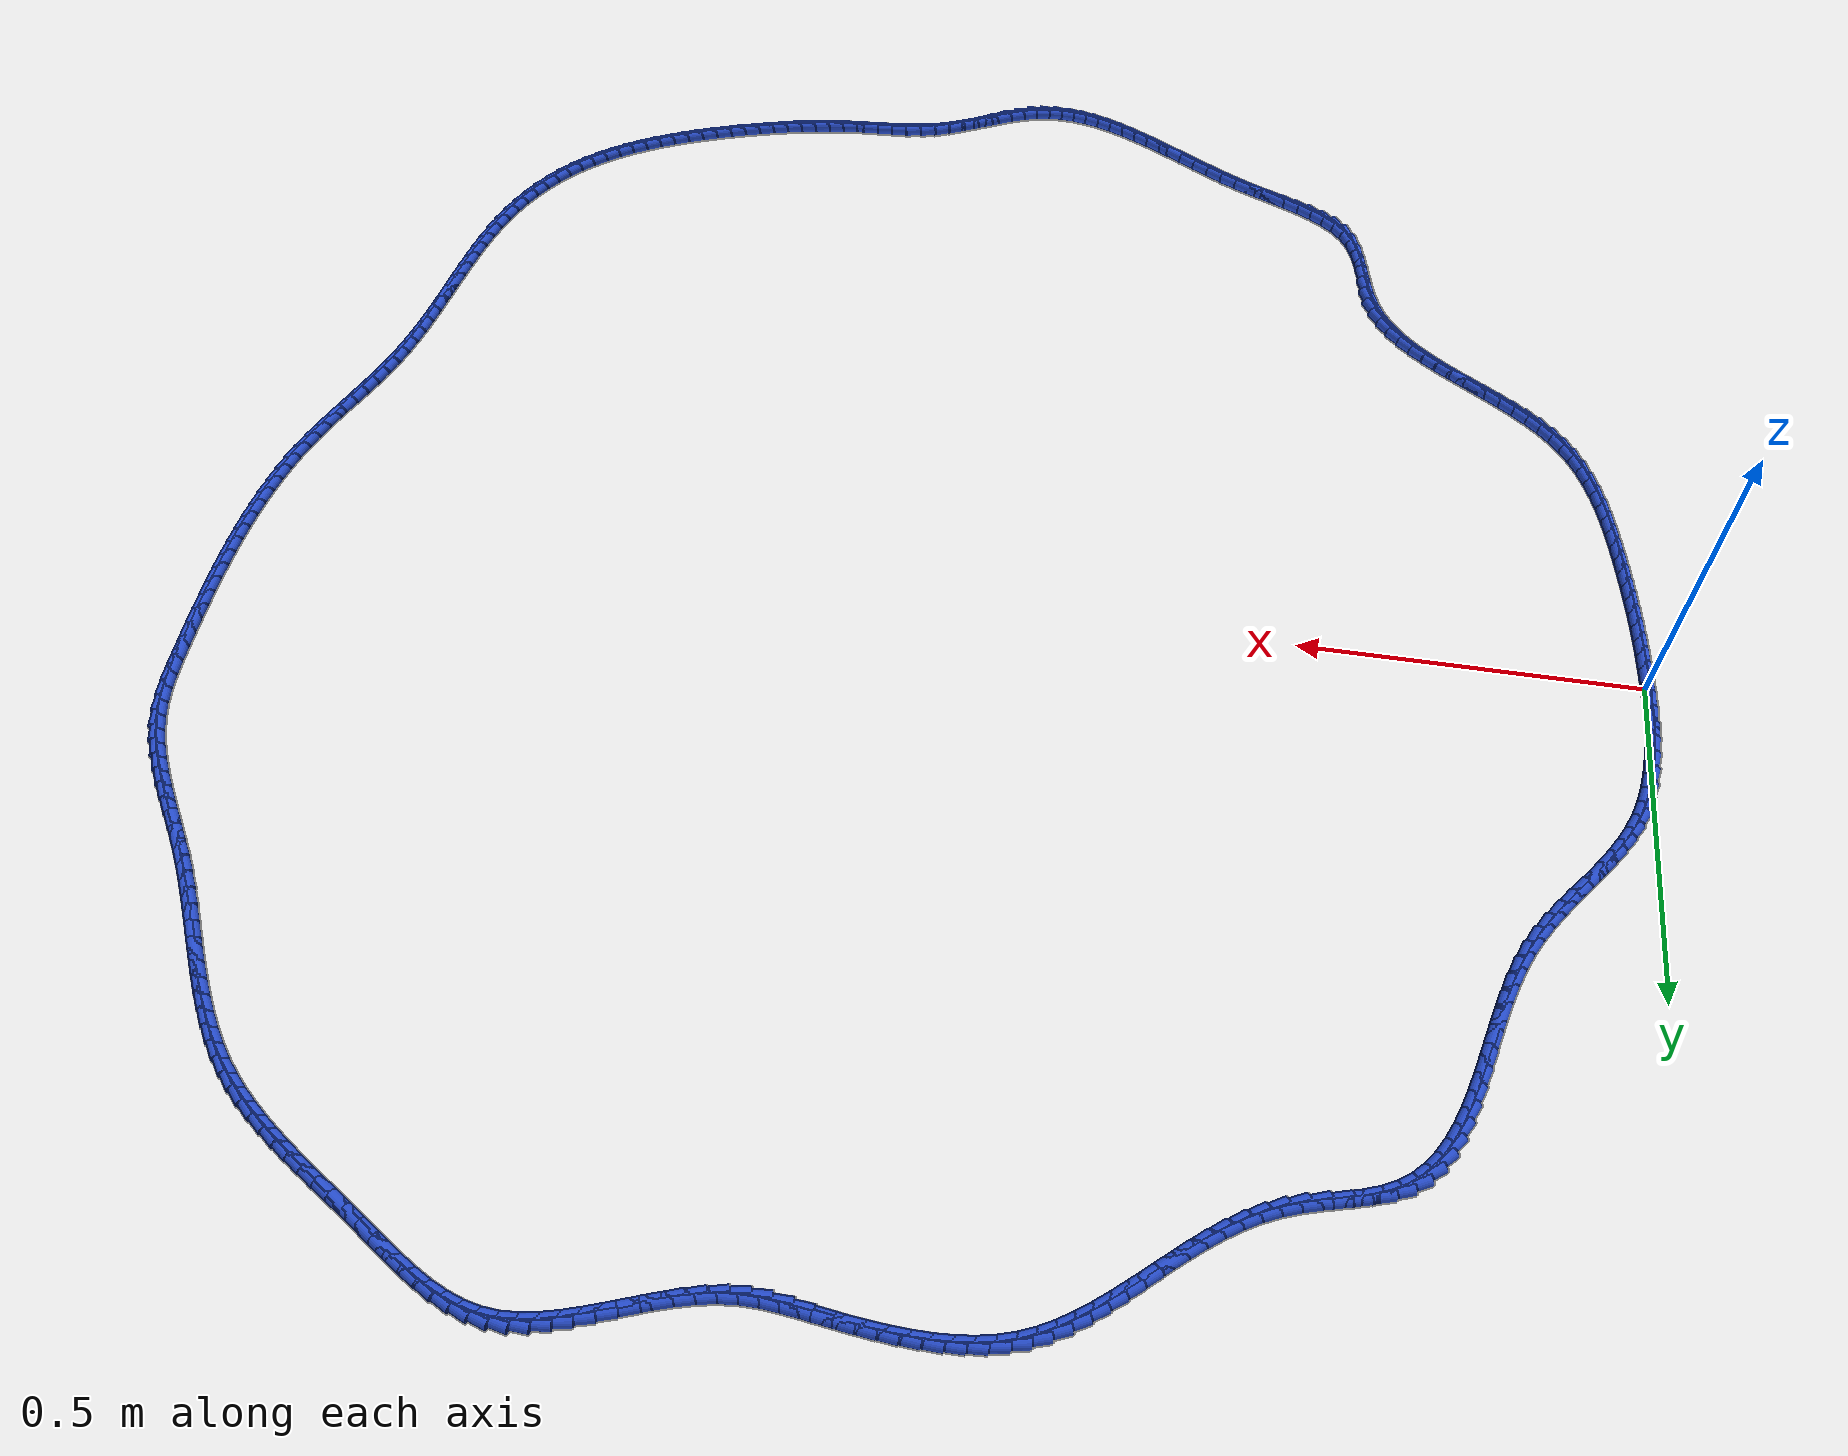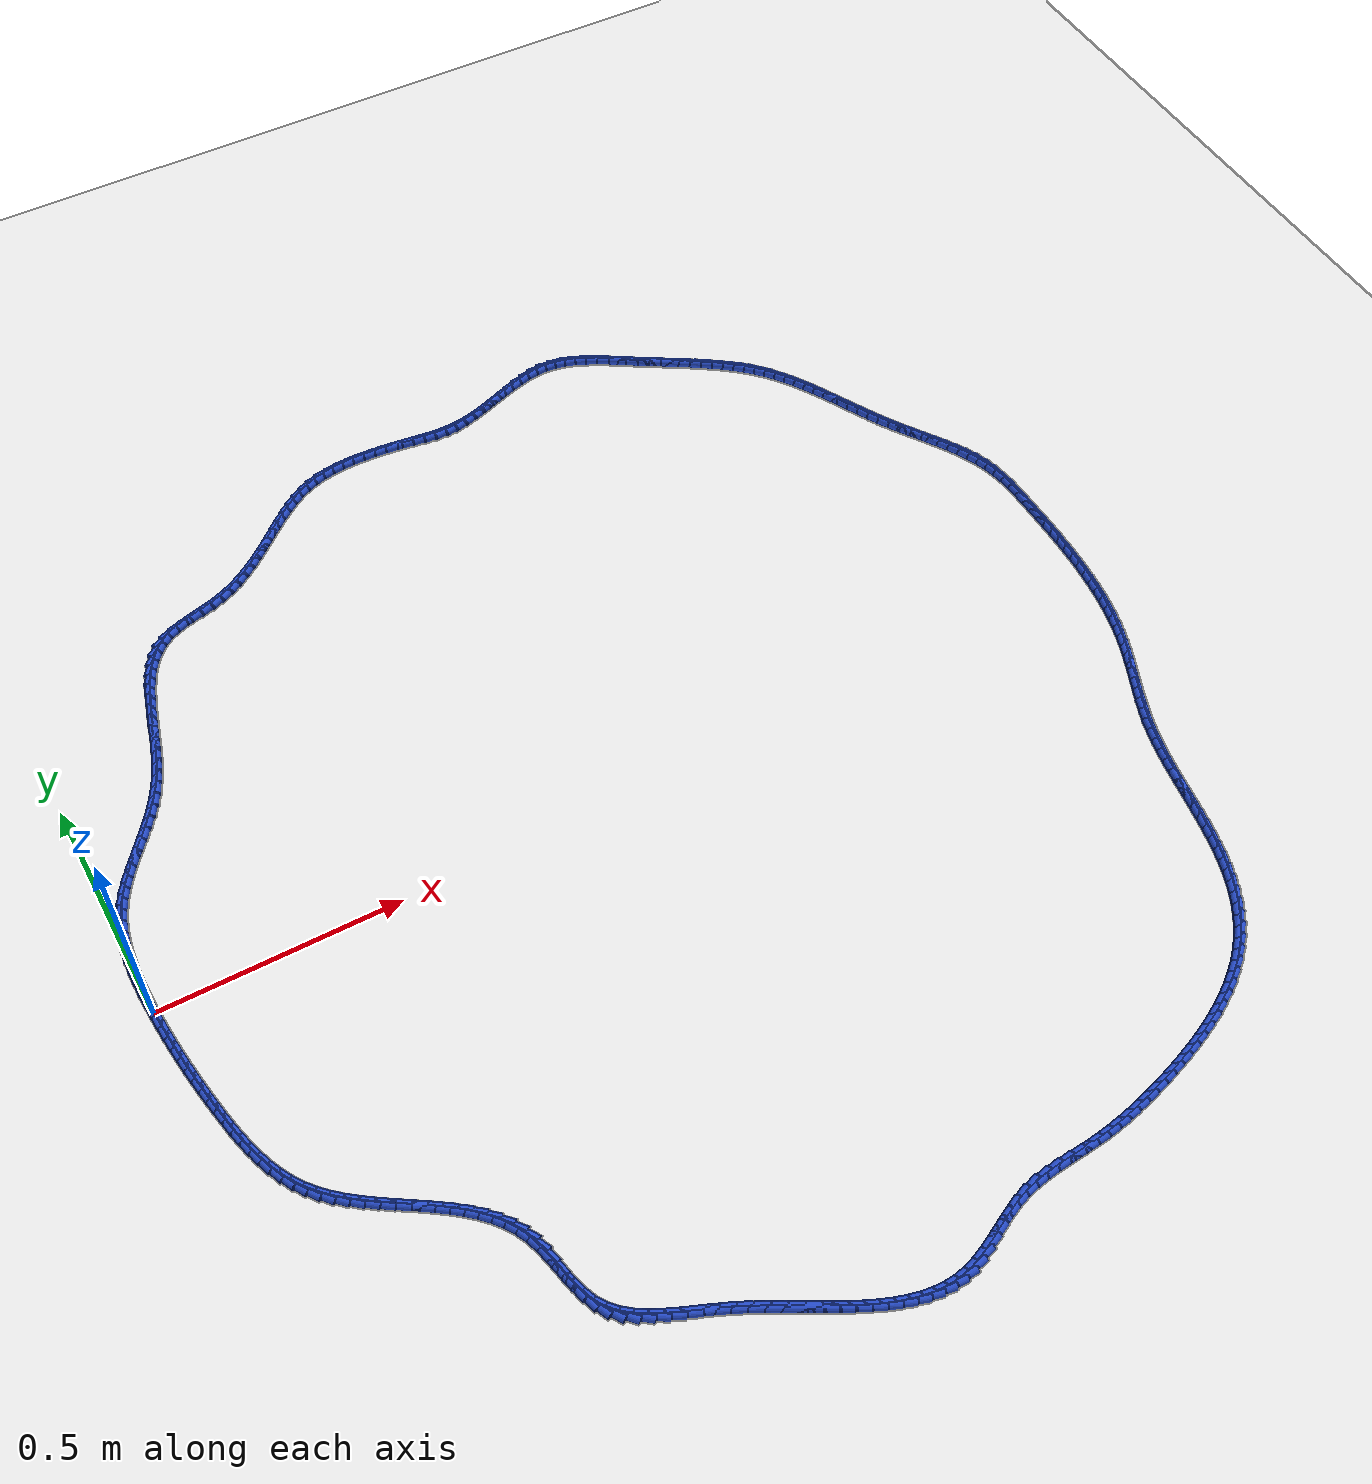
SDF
<sdf version="1.6">
 <world name="default">
  <light name="sun" type="directional">
   <pose>0 0 10 0 -0 0</pose>
   <diffuse>0.8 0.8 0.8 1</diffuse>
   <specular>0.2 0.2 0.2 1</specular>
   <attenuation>
    <range>1000</range>
    <constant>0.9</constant>
    <linear>0.01</linear>
    <quadratic>0.001</quadratic>
   </attenuation>
   <direction>-0.5 0.1 -0.9</direction>
  </light>
  <model name="ground_plane">
   <static>1</static>
   <link name="link">
    <collision name="collision">
     <geometry><plane><normal>0 0 1</normal><size>100 100</size></plane></geometry>
     <surface><friction><ode><mu>100</mu><mu2>50</mu2></ode></friction></surface>
    </collision>
    <visual name="visual">
     <cast_shadows>0</cast_shadows>
     <geometry><plane><normal>0 0 1</normal><size>100 100</size></plane></geometry>
     <material>
      <script><uri>file://media/materials/scripts/gazebo.material</uri><name>Gazebo/WhiteGlow</name></script>
     </material>
    </visual>
   </link>
  </model>
  <gravity>0 0 -9.8</gravity>
  <magnetic_field>6e-06 2.3e-05 -4.2e-05</magnetic_field>
  <atmosphere type="adiabatic"/>
  <physics name="default_physics" default="0" type="ode">
   <max_step_size>0.001</max_step_size>
   <real_time_factor>1</real_time_factor>
   <real_time_update_rate>1000</real_time_update_rate>
  </physics>
  <scene><ambient>0.4 0.4 0.4 1</ambient><background>0.7 0.7 0.7 1</background><shadows>1</shadows></scene>
  <spherical_coordinates>
   <surface_model>EARTH_WGS84</surface_model>
   <latitude_deg>0</latitude_deg>
   <longitude_deg>0</longitude_deg>
   <elevation>0</elevation>
   <heading_deg>0</heading_deg>
  </spherical_coordinates>
  <model name="line">
   <link name="link_0">
    <pose>7.589415207398531e-18 -2.0816681711721685e-17 0.01 0 1.57 -1.529208545914777</pose>
    <collision name="collision">
     <geometry><cylinder><radius>0.01</radius><length>0.08</length></cylinder></geometry>
    </collision>
    <visual name="visual">
     <material>
      <script><name>Gazebo/Blue</name><uri>file://media/materials/scripts/gazebo.material</uri></script>
     </material>
     <geometry><cylinder><radius>0.01</radius><length>0.08</length></cylinder></geometry>
    </visual>
   </link>
   <link name="link_1">
    <pose>-0.001078734033683846 0.025923769754715248 0.01 0 1.57 -1.5508371262471419</pose>
    <collision name="collision">
     <geometry><cylinder><radius>0.01</radius><length>0.08</length></cylinder></geometry>
    </collision>
    <visual name="visual">
     <material>
      <script><name>Gazebo/Blue</name><uri>file://media/materials/scripts/gazebo.material</uri></script>
     </material>
     <geometry><cylinder><radius>0.01</radius><length>0.08</length></cylinder></geometry>
    </visual>
   </link>
   <link name="link_2">
    <pose>-0.0015996408604705913 0.05201888576601871 0.01 0 1.57 1.5625225211086227</pose>
    <collision name="collision">
     <geometry><cylinder><radius>0.01</radius><length>0.08</length></cylinder></geometry>
    </collision>
    <visual name="visual">
     <material>
      <script><name>Gazebo/Blue</name><uri>file://media/materials/scripts/gazebo.material</uri></script>
     </material>
     <geometry><cylinder><radius>0.01</radius><length>0.08</length></cylinder></geometry>
    </visual>
   </link>
   <link name="link_3">
    <pose>-0.0013835428001166047 0.07813662861202465 0.01 0 1.57 1.527260607950316</pose>
    <collision name="collision">
     <geometry><cylinder><radius>0.01</radius><length>0.08</length></cylinder></geometry>
    </collision>
    <visual name="visual">
     <material>
      <script><name>Gazebo/Blue</name><uri>file://media/materials/scripts/gazebo.material</uri></script>
     </material>
     <geometry><cylinder><radius>0.01</radius><length>0.08</length></cylinder></geometry>
    </visual>
   </link>
   <link name="link_4">
    <pose>-0.00025126217237826567 0.10412827887084732 0.01 0 1.57 1.4843901281129186</pose>
    <collision name="collision">
     <geometry><cylinder><radius>0.01</radius><length>0.08</length></cylinder></geometry>
    </collision>
    <visual name="visual">
     <material>
      <script><name>Gazebo/Blue</name><uri>file://media/materials/scripts/gazebo.material</uri></script>
     </material>
     <geometry><cylinder><radius>0.01</radius><length>0.08</length></cylinder></geometry>
    </visual>
   </link>
   <link name="link_5">
    <pose>0.001976378702988048 0.12984511712060098 0.01 0 1.57 1.433208479762104</pose>
    <collision name="collision">
     <geometry><cylinder><radius>0.01</radius><length>0.08</length></cylinder></geometry>
    </collision>
    <visual name="visual">
     <material>
      <script><name>Gazebo/Blue</name><uri>file://media/materials/scripts/gazebo.material</uri></script>
     </material>
     <geometry><cylinder><radius>0.01</radius><length>0.08</length></cylinder></geometry>
    </visual>
   </link>
   <link name="link_6">
    <pose>0.005478557506225959 0.15513842393939994 0.01 0 1.57 1.3729463833635678</pose>
    <collision name="collision">
     <geometry><cylinder><radius>0.01</radius><length>0.08</length></cylinder></geometry>
    </collision>
    <visual name="visual">
     <material>
      <script><name>Gazebo/Blue</name><uri>file://media/materials/scripts/gazebo.material</uri></script>
     </material>
     <geometry><cylinder><radius>0.01</radius><length>0.08</length></cylinder></geometry>
    </visual>
   </link>
   <link name="link_7">
    <pose>0.010434451917579086 0.17985947990535844 0.01 0 1.57 1.302865412017237</pose>
    <collision name="collision">
     <geometry><cylinder><radius>0.01</radius><length>0.08</length></cylinder></geometry>
    </collision>
    <visual name="visual">
     <material>
      <script><name>Gazebo/Blue</name><uri>file://media/materials/scripts/gazebo.material</uri></script>
     </material>
     <geometry><cylinder><radius>0.01</radius><length>0.08</length></cylinder></geometry>
    </visual>
   </link>
   <link name="link_8">
    <pose>0.017023239617291054 0.2038595655965908 0.01 0 1.57 1.2224146423385887</pose>
    <collision name="collision">
     <geometry><cylinder><radius>0.01</radius><length>0.08</length></cylinder></geometry>
    </collision>
    <visual name="visual">
     <material>
      <script><name>Gazebo/Blue</name><uri>file://media/materials/scripts/gazebo.material</uri></script>
     </material>
     <geometry><cylinder><radius>0.01</radius><length>0.08</length></cylinder></geometry>
    </visual>
   </link>
   <link name="link_9">
    <pose>0.025424098285605476 0.2269899615912112 0.01 0 1.57 1.1339320984130088</pose>
    <collision name="collision">
     <geometry><cylinder><radius>0.01</radius><length>0.08</length></cylinder></geometry>
    </collision>
    <visual name="visual">
     <material>
      <script><name>Gazebo/Blue</name><uri>file://media/materials/scripts/gazebo.material</uri></script>
     </material>
     <geometry><cylinder><radius>0.01</radius><length>0.08</length></cylinder></geometry>
    </visual>
   </link>
   <link name="link_10">
    <pose>0.03576604186182409 0.24913756643101184 0.01 0 1.57 1.0544029692733932</pose>
    <collision name="collision">
     <geometry><cylinder><radius>0.01</radius><length>0.08</length></cylinder></geometry>
    </collision>
    <visual name="visual">
     <material>
      <script><name>Gazebo/Blue</name><uri>file://media/materials/scripts/gazebo.material</uri></script>
     </material>
     <geometry><cylinder><radius>0.01</radius><length>0.08</length></cylinder></geometry>
    </visual>
   </link>
   <link name="link_11">
    <pose>0.04785078753249368 0.27042167049365284 0.01 0 1.57 0.9914801807485655</pose>
    <collision name="collision">
     <geometry><cylinder><radius>0.01</radius><length>0.08</length></cylinder></geometry>
    </collision>
    <visual name="visual">
     <material>
      <script><name>Gazebo/Blue</name><uri>file://media/materials/scripts/gazebo.material</uri></script>
     </material>
     <geometry><cylinder><radius>0.01</radius><length>0.08</length></cylinder></geometry>
    </visual>
   </link>
   <link name="link_12">
    <pose>0.06134878479980714 0.29105476868113006 0.01 0 1.57 0.945435414971339</pose>
    <collision name="collision">
     <geometry><cylinder><radius>0.01</radius><length>0.08</length></cylinder></geometry>
    </collision>
    <visual name="visual">
     <material>
      <script><name>Gazebo/Blue</name><uri>file://media/materials/scripts/gazebo.material</uri></script>
     </material>
     <geometry><cylinder><radius>0.01</radius><length>0.08</length></cylinder></geometry>
    </visual>
   </link>
   <link name="link_13">
    <pose>0.07593013106613243 0.31124960589830053 0.01 0 1.57 0.9159262423894816</pose>
    <collision name="collision">
     <geometry><cylinder><radius>0.01</radius><length>0.08</length></cylinder></geometry>
    </collision>
    <visual name="visual">
     <material>
      <script><name>Gazebo/Blue</name><uri>file://media/materials/scripts/gazebo.material</uri></script>
     </material>
     <geometry><cylinder><radius>0.01</radius><length>0.08</length></cylinder></geometry>
    </visual>
   </link>
   <link name="link_14">
    <pose>0.0912649237338376 0.33121892705002176 0.01 0 1.57 0.9024092016209881</pose>
    <collision name="collision">
     <geometry><cylinder><radius>0.01</radius><length>0.08</length></cylinder></geometry>
    </collision>
    <visual name="visual">
     <material>
      <script><name>Gazebo/Blue</name><uri>file://media/materials/scripts/gazebo.material</uri></script>
     </material>
     <geometry><cylinder><radius>0.01</radius><length>0.08</length></cylinder></geometry>
    </visual>
   </link>
   <link name="link_15">
    <pose>0.10702326020529049 0.3511754770411508 0.01 0 1.57 0.904376053428347</pose>
    <collision name="collision">
     <geometry><cylinder><radius>0.01</radius><length>0.08</length></cylinder></geometry>
    </collision>
    <visual name="visual">
     <material>
      <script><name>Gazebo/Blue</name><uri>file://media/materials/scripts/gazebo.material</uri></script>
     </material>
     <geometry><cylinder><radius>0.01</radius><length>0.08</length></cylinder></geometry>
    </visual>
   </link>
   <link name="link_16">
    <pose>0.12287523788285908 0.371332000776545 0.01 0 1.57 0.9214471286484537</pose>
    <collision name="collision">
     <geometry><cylinder><radius>0.01</radius><length>0.08</length></cylinder></geometry>
    </collision>
    <visual name="visual">
     <material>
      <script><name>Gazebo/Blue</name><uri>file://media/materials/scripts/gazebo.material</uri></script>
     </material>
     <geometry><cylinder><radius>0.01</radius><length>0.08</length></cylinder></geometry>
    </visual>
   </link>
   <link name="link_17">
    <pose>0.13849095416891138 0.3919012431610617 0.01 0 1.57 0.9533493094105094</pose>
    <collision name="collision">
     <geometry><cylinder><radius>0.01</radius><length>0.08</length></cylinder></geometry>
    </collision>
    <visual name="visual">
     <material>
      <script><name>Gazebo/Blue</name><uri>file://media/materials/scripts/gazebo.material</uri></script>
     </material>
     <geometry><cylinder><radius>0.01</radius><length>0.08</length></cylinder></geometry>
    </visual>
   </link>
   <link name="link_18">
    <pose>0.1535405064658153 0.4130959490995578 0.01 0 1.57 0.9997971107590262</pose>
    <collision name="collision">
     <geometry><cylinder><radius>0.01</radius><length>0.08</length></cylinder></geometry>
    </collision>
    <visual name="visual">
     <material>
      <script><name>Gazebo/Blue</name><uri>file://media/materials/scripts/gazebo.material</uri></script>
     </material>
     <geometry><cylinder><radius>0.01</radius><length>0.08</length></cylinder></geometry>
    </visual>
   </link>
   <link name="link_19">
    <pose>0.1676939921759389 0.43512886349689106 0.01 0 1.57 1.060289847884883</pose>
    <collision name="collision">
     <geometry><cylinder><radius>0.01</radius><length>0.08</length></cylinder></geometry>
    </collision>
    <visual name="visual">
     <material>
      <script><name>Gazebo/Blue</name><uri>file://media/materials/scripts/gazebo.material</uri></script>
     </material>
     <geometry><cylinder><radius>0.01</radius><length>0.08</length></cylinder></geometry>
    </visual>
   </link>
   <link name="link_20">
    <pose>0.18062150870164997 0.4582127312579184 0.01 0 1.57 1.1304237792960314</pose>
    <collision name="collision">
     <geometry><cylinder><radius>0.01</radius><length>0.08</length></cylinder></geometry>
    </collision>
    <visual name="visual">
     <material>
      <script><name>Gazebo/Blue</name><uri>file://media/materials/scripts/gazebo.material</uri></script>
     </material>
     <geometry><cylinder><radius>0.01</radius><length>0.08</length></cylinder></geometry>
    </visual>
   </link>
   <link name="link_21">
    <pose>0.19206698702457214 0.4825009542034054 0.01 0 1.57 1.1908884326159306</pose>
    <collision name="collision">
     <geometry><cylinder><radius>0.01</radius><length>0.08</length></cylinder></geometry>
    </collision>
    <visual name="visual">
     <material>
      <script><name>Gazebo/Blue</name><uri>file://media/materials/scripts/gazebo.material</uri></script>
     </material>
     <geometry><cylinder><radius>0.01</radius><length>0.08</length></cylinder></geometry>
    </visual>
   </link>
   <link name="link_22">
    <pose>0.20217802614665786 0.5078224895651227 0.01 0 1.57 1.2363188396179854</pose>
    <collision name="collision">
     <geometry><cylinder><radius>0.01</radius><length>0.08</length></cylinder></geometry>
    </collision>
    <visual name="visual">
     <material>
      <script><name>Gazebo/Blue</name><uri>file://media/materials/scripts/gazebo.material</uri></script>
     </material>
     <geometry><cylinder><radius>0.01</radius><length>0.08</length></cylinder></geometry>
    </visual>
   </link>
   <link name="link_23">
    <pose>0.21123948446984714 0.5338959735502072 0.01 0 1.57 1.2678477357379563</pose>
    <collision name="collision">
     <geometry><cylinder><radius>0.01</radius><length>0.08</length></cylinder></geometry>
    </collision>
    <visual name="visual">
     <material>
      <script><name>Gazebo/Blue</name><uri>file://media/materials/scripts/gazebo.material</uri></script>
     </material>
     <geometry><cylinder><radius>0.01</radius><length>0.08</length></cylinder></geometry>
    </visual>
   </link>
   <link name="link_24">
    <pose>0.21953633408978057 0.5604399509854932 0.01 0 1.57 1.286309996812792</pose>
    <collision name="collision">
     <geometry><cylinder><radius>0.01</radius><length>0.08</length></cylinder></geometry>
    </collision>
    <visual name="visual">
     <material>
      <script><name>Gazebo/Blue</name><uri>file://media/materials/scripts/gazebo.material</uri></script>
     </material>
     <geometry><cylinder><radius>0.01</radius><length>0.08</length></cylinder></geometry>
    </visual>
   </link>
   <link name="link_25">
    <pose>0.2273535471020989 0.5871729666978145 0.01 0 1.57 1.2921167434524472</pose>
    <collision name="collision">
     <geometry><cylinder><radius>0.01</radius><length>0.08</length></cylinder></geometry>
    </collision>
    <visual name="visual">
     <material>
      <script><name>Gazebo/Blue</name><uri>file://media/materials/scripts/gazebo.material</uri></script>
     </material>
     <geometry><cylinder><radius>0.01</radius><length>0.08</length></cylinder></geometry>
    </visual>
   </link>
   <link name="link_26">
    <pose>0.23497609560244256 0.6138135655140053 0.01 0 1.57 1.285188259427947</pose>
    <collision name="collision">
     <geometry><cylinder><radius>0.01</radius><length>0.08</length></cylinder></geometry>
    </collision>
    <visual name="visual">
     <material>
      <script><name>Gazebo/Blue</name><uri>file://media/materials/scripts/gazebo.material</uri></script>
     </material>
     <geometry><cylinder><radius>0.01</radius><length>0.08</length></cylinder></geometry>
    </visual>
   </link>
   <link name="link_27">
    <pose>0.24268895168645244 0.6400802922608996 0.01 0 1.57 1.2649059024992504</pose>
    <collision name="collision">
     <geometry><cylinder><radius>0.01</radius><length>0.08</length></cylinder></geometry>
    </collision>
    <visual name="visual">
     <material>
      <script><name>Gazebo/Blue</name><uri>file://media/materials/scripts/gazebo.material</uri></script>
     </material>
     <geometry><cylinder><radius>0.01</radius><length>0.08</length></cylinder></geometry>
    </visual>
   </link>
   <link name="link_28">
    <pose>0.25077708744976906 0.6656916917653314 0.01 0 1.57 1.230073746133724</pose>
    <collision name="collision">
     <geometry><cylinder><radius>0.01</radius><length>0.08</length></cylinder></geometry>
    </collision>
    <visual name="visual">
     <material>
      <script><name>Gazebo/Blue</name><uri>file://media/materials/scripts/gazebo.material</uri></script>
     </material>
     <geometry><cylinder><radius>0.01</radius><length>0.08</length></cylinder></geometry>
    </visual>
   </link>
   <link name="link_29">
    <pose>0.2595254749880331 0.6903663088541351 0.01 0 1.57 1.1789104156207686</pose>
    <collision name="collision">
     <geometry><cylinder><radius>0.01</radius><length>0.08</length></cylinder></geometry>
    </collision>
    <visual name="visual">
     <material>
      <script><name>Gazebo/Blue</name><uri>file://media/materials/scripts/gazebo.material</uri></script>
     </material>
     <geometry><cylinder><radius>0.01</radius><length>0.08</length></cylinder></geometry>
    </visual>
   </link>
   <link name="link_30">
    <pose>0.2692190863968851 0.713822688354144 0.01 0 1.57 1.1091377304011967</pose>
    <collision name="collision">
     <geometry><cylinder><radius>0.01</radius><length>0.08</length></cylinder></geometry>
    </collision>
    <visual name="visual">
     <material>
      <script><name>Gazebo/Blue</name><uri>file://media/materials/scripts/gazebo.material</uri></script>
     </material>
     <geometry><cylinder><radius>0.01</radius><length>0.08</length></cylinder></geometry>
    </visual>
   </link>
   <link name="link_31">
    <pose>0.2801428937719657 0.7357793750921923 0.01 0 1.57 1.0183055914703059</pose>
    <collision name="collision">
     <geometry><cylinder><radius>0.01</radius><length>0.08</length></cylinder></geometry>
    </collision>
    <visual name="visual">
     <material>
      <script><name>Gazebo/Blue</name><uri>file://media/materials/scripts/gazebo.material</uri></script>
     </material>
     <geometry><cylinder><radius>0.01</radius><length>0.08</length></cylinder></geometry>
    </visual>
   </link>
   <link name="link_32">
    <pose>0.29258186920891577 0.7559549138951146 0.01 0 1.57 0.9045703298850295</pose>
    <collision name="collision">
     <geometry><cylinder><radius>0.01</radius><length>0.08</length></cylinder></geometry>
    </collision>
    <visual name="visual">
     <material>
      <script><name>Gazebo/Blue</name><uri>file://media/materials/scripts/gazebo.material</uri></script>
     </material>
     <geometry><cylinder><radius>0.01</radius><length>0.08</length></cylinder></geometry>
    </visual>
   </link>
   <link name="link_33">
    <pose>0.3068209848033757 0.7740678495897444 0.01 0 1.57 0.7680955369178402</pose>
    <collision name="collision">
     <geometry><cylinder><radius>0.01</radius><length>0.08</length></cylinder></geometry>
    </collision>
    <visual name="visual">
     <material>
      <script><name>Gazebo/Blue</name><uri>file://media/materials/scripts/gazebo.material</uri></script>
     </material>
     <geometry><cylinder><radius>0.01</radius><length>0.08</length></cylinder></geometry>
    </visual>
   </link>
   <link name="link_34">
    <pose>0.32314521265098634 0.7898367270029163 0.01 0 1.57 0.6127817458885213</pose>
    <collision name="collision">
     <geometry><cylinder><radius>0.01</radius><length>0.08</length></cylinder></geometry>
    </collision>
    <visual name="visual">
     <material>
      <script><name>Gazebo/Blue</name><uri>file://media/materials/scripts/gazebo.material</uri></script>
     </material>
     <geometry><cylinder><radius>0.01</radius><length>0.08</length></cylinder></geometry>
    </visual>
   </link>
   <link name="link_35">
    <pose>0.3418395248473881 0.8029800909614637 0.01 0 1.57 0.4562331163374501</pose>
    <collision name="collision">
     <geometry><cylinder><radius>0.01</radius><length>0.08</length></cylinder></geometry>
    </collision>
    <visual name="visual">
     <material>
      <script><name>Gazebo/Blue</name><uri>file://media/materials/scripts/gazebo.material</uri></script>
     </material>
     <geometry><cylinder><radius>0.01</radius><length>0.08</length></cylinder></geometry>
    </visual>
   </link>
   <link name="link_36">
    <pose>0.3630480060579663 0.813388491345508 0.01 0 1.57 0.34513263830318064</pose>
    <collision name="collision">
     <geometry><cylinder><radius>0.01</radius><length>0.08</length></cylinder></geometry>
    </collision>
    <visual name="visual">
     <material>
      <script><name>Gazebo/Blue</name><uri>file://media/materials/scripts/gazebo.material</uri></script>
     </material>
     <geometry><cylinder><radius>0.01</radius><length>0.08</length></cylinder></geometry>
    </visual>
   </link>
   <link name="link_37">
    <pose>0.3862714589177586 0.8217378409288465 0.01 0 1.57 0.28485016910019423</pose>
    <collision name="collision">
     <geometry><cylinder><radius>0.01</radius><length>0.08</length></cylinder></geometry>
    </collision>
    <visual name="visual">
     <material>
      <script><name>Gazebo/Blue</name><uri>file://media/materials/scripts/gazebo.material</uri></script>
     </material>
     <geometry><cylinder><radius>0.01</radius><length>0.08</length></cylinder></geometry>
    </visual>
   </link>
   <link name="link_38">
    <pose>0.41082719057515144 0.8289280763808236 0.01 0 1.57 0.2683520575616517</pose>
    <collision name="collision">
     <geometry><cylinder><radius>0.01</radius><length>0.08</length></cylinder></geometry>
    </collision>
    <visual name="visual">
     <material>
      <script><name>Gazebo/Blue</name><uri>file://media/materials/scripts/gazebo.material</uri></script>
     </material>
     <geometry><cylinder><radius>0.01</radius><length>0.08</length></cylinder></geometry>
    </visual>
   </link>
   <link name="link_39">
    <pose>0.436032494384066 0.8358591512120139 0.01 0 1.57 0.29219346268174373</pose>
    <collision name="collision">
     <geometry><cylinder><radius>0.01</radius><length>0.08</length></cylinder></geometry>
    </collision>
    <visual name="visual">
     <material>
      <script><name>Gazebo/Blue</name><uri>file://media/materials/scripts/gazebo.material</uri></script>
     </material>
     <geometry><cylinder><radius>0.01</radius><length>0.08</length></cylinder></geometry>
    </visual>
   </link>
   <link name="link_40">
    <pose>0.46120466369842356 0.843431018932993 0.01 0 1.57 0.35649394090297615</pose>
    <collision name="collision">
     <geometry><cylinder><radius>0.01</radius><length>0.08</length></cylinder></geometry>
    </collision>
    <visual name="visual">
     <material>
      <script><name>Gazebo/Blue</name><uri>file://media/materials/scripts/gazebo.material</uri></script>
     </material>
     <geometry><cylinder><radius>0.01</radius><length>0.08</length></cylinder></geometry>
    </visual>
   </link>
   <link name="link_41">
    <pose>0.4856637001289965 0.8525396941326364 0.01 0 1.57 0.44537588618805934</pose>
    <collision name="collision">
     <geometry><cylinder><radius>0.01</radius><length>0.08</length></cylinder></geometry>
    </collision>
    <visual name="visual">
     <material>
      <script><name>Gazebo/Blue</name><uri>file://media/materials/scripts/gazebo.material</uri></script>
     </material>
     <geometry><cylinder><radius>0.01</radius><length>0.08</length></cylinder></geometry>
    </visual>
   </link>
   <link name="link_42">
    <pose>0.5090043006838957 0.8636816710734182 0.01 0 1.57 0.5251237709512133</pose>
    <collision name="collision">
     <geometry><cylinder><radius>0.01</radius><length>0.08</length></cylinder></geometry>
    </collision>
    <visual name="visual">
     <material>
      <script><name>Gazebo/Blue</name><uri>file://media/materials/scripts/gazebo.material</uri></script>
     </material>
     <geometry><cylinder><radius>0.01</radius><length>0.08</length></cylinder></geometry>
    </visual>
   </link>
   <link name="link_43">
    <pose>0.5313282934927702 0.8766158663475309 0.01 0 1.57 0.5911054244074284</pose>
    <collision name="collision">
     <geometry><cylinder><radius>0.01</radius><length>0.08</length></cylinder></geometry>
    </collision>
    <visual name="visual">
     <material>
      <script><name>Gazebo/Blue</name><uri>file://media/materials/scripts/gazebo.material</uri></script>
     </material>
     <geometry><cylinder><radius>0.01</radius><length>0.08</length></cylinder></geometry>
    </visual>
   </link>
   <link name="link_44">
    <pose>0.5527922540091227 0.8910215713735858 0.01 0 1.57 0.6430733423428566</pose>
    <collision name="collision">
     <geometry><cylinder><radius>0.01</radius><length>0.08</length></cylinder></geometry>
    </collision>
    <visual name="visual">
     <material>
      <script><name>Gazebo/Blue</name><uri>file://media/materials/scripts/gazebo.material</uri></script>
     </material>
     <geometry><cylinder><radius>0.01</radius><length>0.08</length></cylinder></geometry>
    </visual>
   </link>
   <link name="link_45">
    <pose>0.5735527576864544 0.9065780775701938 0.01 0 1.57 0.6812139061971629</pose>
    <collision name="collision">
     <geometry><cylinder><radius>0.01</radius><length>0.08</length></cylinder></geometry>
    </collision>
    <visual name="visual">
     <material>
      <script><name>Gazebo/Blue</name><uri>file://media/materials/scripts/gazebo.material</uri></script>
     </material>
     <geometry><cylinder><radius>0.01</radius><length>0.08</length></cylinder></geometry>
    </visual>
   </link>
   <link name="link_46">
    <pose>0.5937663799782674 0.9229646763559662 0.01 0 1.57 0.705844480868185</pose>
    <collision name="collision">
     <geometry><cylinder><radius>0.01</radius><length>0.08</length></cylinder></geometry>
    </collision>
    <visual name="visual">
     <material>
      <script><name>Gazebo/Blue</name><uri>file://media/materials/scripts/gazebo.material</uri></script>
     </material>
     <geometry><cylinder><radius>0.01</radius><length>0.08</length></cylinder></geometry>
    </visual>
   </link>
   <link name="link_47">
    <pose>0.6135896963380639 0.9398606591495142 0.01 0 1.57 0.7172019870252846</pose>
    <collision name="collision">
     <geometry><cylinder><radius>0.01</radius><length>0.08</length></cylinder></geometry>
    </collision>
    <visual name="visual">
     <material>
      <script><name>Gazebo/Blue</name><uri>file://media/materials/scripts/gazebo.material</uri></script>
     </material>
     <geometry><cylinder><radius>0.01</radius><length>0.08</length></cylinder></geometry>
    </visual>
   </link>
   <link name="link_48">
    <pose>0.6331792822193455 0.9569453173694485 0.01 0 1.57 0.7153142622757979</pose>
    <collision name="collision">
     <geometry><cylinder><radius>0.01</radius><length>0.08</length></cylinder></geometry>
    </collision>
    <visual name="visual">
     <material>
      <script><name>Gazebo/Blue</name><uri>file://media/materials/scripts/gazebo.material</uri></script>
     </material>
     <geometry><cylinder><radius>0.01</radius><length>0.08</length></cylinder></geometry>
    </visual>
   </link>
   <link name="link_49">
    <pose>0.6526917130756145 0.9738979424343805 0.01 0 1.57 0.6999371337386757</pose>
    <collision name="collision">
     <geometry><cylinder><radius>0.01</radius><length>0.08</length></cylinder></geometry>
    </collision>
    <visual name="visual">
     <material>
      <script><name>Gazebo/Blue</name><uri>file://media/materials/scripts/gazebo.material</uri></script>
     </material>
     <geometry><cylinder><radius>0.01</radius><length>0.08</length></cylinder></geometry>
    </visual>
   </link>
   <link name="link_50">
    <pose>0.6722835643603724 0.9903978257629216 0.01 0 1.57 0.6705493919131295</pose>
    <collision name="collision">
     <geometry><cylinder><radius>0.01</radius><length>0.08</length></cylinder></geometry>
    </collision>
    <visual name="visual">
     <material>
      <script><name>Gazebo/Blue</name><uri>file://media/materials/scripts/gazebo.material</uri></script>
     </material>
     <geometry><cylinder><radius>0.01</radius><length>0.08</length></cylinder></geometry>
    </visual>
   </link>
   <link name="link_51">
    <pose>0.6921114115271211 1.006124258773682 0.01 0 1.57 0.6264152194766989</pose>
    <collision name="collision">
     <geometry><cylinder><radius>0.01</radius><length>0.08</length></cylinder></geometry>
    </collision>
    <visual name="visual">
     <material>
      <script><name>Gazebo/Blue</name><uri>file://media/materials/scripts/gazebo.material</uri></script>
     </material>
     <geometry><cylinder><radius>0.01</radius><length>0.08</length></cylinder></geometry>
    </visual>
   </link>
   <link name="link_52">
    <pose>0.7123318300293627 1.0207565328852735 0.01 0 1.57 0.5667432863231895</pose>
    <collision name="collision">
     <geometry><cylinder><radius>0.01</radius><length>0.08</length></cylinder></geometry>
    </collision>
    <visual name="visual">
     <material>
      <script><name>Gazebo/Blue</name><uri>file://media/materials/scripts/gazebo.material</uri></script>
     </material>
     <geometry><cylinder><radius>0.01</radius><length>0.08</length></cylinder></geometry>
    </visual>
   </link>
   <link name="link_53">
    <pose>0.7331013953205993 1.033973939516307 0.01 0 1.57 0.49098431802284925</pose>
    <collision name="collision">
     <geometry><cylinder><radius>0.01</radius><length>0.08</length></cylinder></geometry>
    </collision>
    <visual name="visual">
     <material>
      <script><name>Gazebo/Blue</name><uri>file://media/materials/scripts/gazebo.material</uri></script>
     </material>
     <geometry><cylinder><radius>0.01</radius><length>0.08</length></cylinder></geometry>
    </visual>
   </link>
   <link name="link_54">
    <pose>0.7545766828543325 1.0454557700853937 0.01 0 1.57 0.3992969907596642</pose>
    <collision name="collision">
     <geometry><cylinder><radius>0.01</radius><length>0.08</length></cylinder></geometry>
    </collision>
    <visual name="visual">
     <material>
      <script><name>Gazebo/Blue</name><uri>file://media/materials/scripts/gazebo.material</uri></script>
     </material>
     <geometry><cylinder><radius>0.01</radius><length>0.08</length></cylinder></geometry>
    </visual>
   </link>
   <link name="link_55">
    <pose>0.7769142116030038 1.0548814207085924 0.01 0 1.57 0.2987789686109148</pose>
    <collision name="collision">
     <geometry><cylinder><radius>0.01</radius><length>0.08</length></cylinder></geometry>
    </collision>
    <visual name="visual">
     <material>
      <script><name>Gazebo/Blue</name><uri>file://media/materials/scripts/gazebo.material</uri></script>
     </material>
     <geometry><cylinder><radius>0.01</radius><length>0.08</length></cylinder></geometry>
    </visual>
   </link>
   <link name="link_56">
    <pose>0.8002034949560083 1.0620544939793517 0.01 0 1.57 0.20780776273310692</pose>
    <collision name="collision">
     <geometry><cylinder><radius>0.01</radius><length>0.08</length></cylinder></geometry>
    </collision>
    <visual name="visual">
     <material>
      <script><name>Gazebo/Blue</name><uri>file://media/materials/scripts/gazebo.material</uri></script>
     </material>
     <geometry><cylinder><radius>0.01</radius><length>0.08</length></cylinder></geometry>
    </visual>
   </link>
   <link name="link_57">
    <pose>0.8243373719606256 1.0671431625182124 0.01 0 1.57 0.12968598027694428</pose>
    <collision name="collision">
     <geometry><cylinder><radius>0.01</radius><length>0.08</length></cylinder></geometry>
    </collision>
    <visual name="visual">
     <material>
      <script><name>Gazebo/Blue</name><uri>file://media/materials/scripts/gazebo.material</uri></script>
     </material>
     <geometry><cylinder><radius>0.01</radius><length>0.08</length></cylinder></geometry>
    </visual>
   </link>
   <link name="link_58">
    <pose>0.849172781782196 1.0703821456075273 0.01 0 1.57 0.06386610277903262</pose>
    <collision name="collision">
     <geometry><cylinder><radius>0.01</radius><length>0.08</length></cylinder></geometry>
    </collision>
    <visual name="visual">
     <material>
      <script><name>Gazebo/Blue</name><uri>file://media/materials/scripts/gazebo.material</uri></script>
     </material>
     <geometry><cylinder><radius>0.01</radius><length>0.08</length></cylinder></geometry>
    </visual>
   </link>
   <link name="link_59">
    <pose>0.8745666635860594 1.0720061625296498 0.01 0 1.57 0.00944476818117881</pose>
    <collision name="collision">
     <geometry><cylinder><radius>0.01</radius><length>0.08</length></cylinder></geometry>
    </collision>
    <visual name="visual">
     <material>
      <script><name>Gazebo/Blue</name><uri>file://media/materials/scripts/gazebo.material</uri></script>
     </material>
     <geometry><cylinder><radius>0.01</radius><length>0.08</length></cylinder></geometry>
    </visual>
   </link>
   <link name="link_60">
    <pose>0.9003759565375553 1.072249932566932 0.01 0 1.57 -0.03456064850577868</pose>
    <collision name="collision">
     <geometry><cylinder><radius>0.01</radius><length>0.08</length></cylinder></geometry>
    </collision>
    <visual name="visual">
     <material>
      <script><name>Gazebo/Blue</name><uri>file://media/materials/scripts/gazebo.material</uri></script>
     </material>
     <geometry><cylinder><radius>0.01</radius><length>0.08</length></cylinder></geometry>
    </visual>
   </link>
   <link name="link_61">
    <pose>0.9264575998020237 1.0713481750017275 0.01 0 1.57 -0.0690431297552558</pose>
    <collision name="collision">
     <geometry><cylinder><radius>0.01</radius><length>0.08</length></cylinder></geometry>
    </collision>
    <visual name="visual">
     <material>
      <script><name>Gazebo/Blue</name><uri>file://media/materials/scripts/gazebo.material</uri></script>
     </material>
     <geometry><cylinder><radius>0.01</radius><length>0.08</length></cylinder></geometry>
    </visual>
   </link>
   <link name="link_62">
    <pose>0.9526685325448041 1.0695356091163883 0.01 0 1.57 -0.09471289323147636</pose>
    <collision name="collision">
     <geometry><cylinder><radius>0.01</radius><length>0.08</length></cylinder></geometry>
    </collision>
    <visual name="visual">
     <material>
      <script><name>Gazebo/Blue</name><uri>file://media/materials/scripts/gazebo.material</uri></script>
     </material>
     <geometry><cylinder><radius>0.01</radius><length>0.08</length></cylinder></geometry>
    </visual>
   </link>
   <link name="link_63">
    <pose>0.9788656939312367 1.067046954193268 0.01 0 1.57 -0.11204745483626488</pose>
    <collision name="collision">
     <geometry><cylinder><radius>0.01</radius><length>0.08</length></cylinder></geometry>
    </collision>
    <visual name="visual">
     <material>
      <script><name>Gazebo/Blue</name><uri>file://media/materials/scripts/gazebo.material</uri></script>
     </material>
     <geometry><cylinder><radius>0.01</radius><length>0.08</length></cylinder></geometry>
    </visual>
   </link>
   <link name="link_64">
    <pose>1.0049060231266613 1.0641169295147193 0.01 0 1.57 -0.120759438822624</pose>
    <collision name="collision">
     <geometry><cylinder><radius>0.01</radius><length>0.08</length></cylinder></geometry>
    </collision>
    <visual name="visual">
     <material>
      <script><name>Gazebo/Blue</name><uri>file://media/materials/scripts/gazebo.material</uri></script>
     </material>
     <geometry><cylinder><radius>0.01</radius><length>0.08</length></cylinder></geometry>
    </visual>
   </link>
   <link name="link_65">
    <pose>1.030652075643724 1.0609926489121884 0.01 0 1.57 -0.1099137533340716</pose>
    <collision name="collision">
     <geometry><cylinder><radius>0.01</radius><length>0.08</length></cylinder></geometry>
    </collision>
    <visual name="visual">
     <material>
      <script><name>Gazebo/Blue</name><uri>file://media/materials/scripts/gazebo.material</uri></script>
     </material>
     <geometry><cylinder><radius>0.01</radius><length>0.08</length></cylinder></geometry>
    </visual>
   </link>
   <link name="link_66">
    <pose>1.056086278800829 1.058185767724326 0.01 0 1.57 -0.06826148288743385</pose>
    <collision name="collision">
     <geometry><cylinder><radius>0.01</radius><length>0.08</length></cylinder></geometry>
    </collision>
    <visual name="visual">
     <material>
      <script><name>Gazebo/Blue</name><uri>file://media/materials/scripts/gazebo.material</uri></script>
     </material>
     <geometry><cylinder><radius>0.01</radius><length>0.08</length></cylinder></geometry>
    </visual>
   </link>
   <link name="link_67">
    <pose>1.0813059798399405 1.0564615546360925 0.01 0 1.57 0.005334337362546125</pose>
    <collision name="collision">
     <geometry><cylinder><radius>0.01</radius><length>0.08</length></cylinder></geometry>
    </collision>
    <visual name="visual">
     <material>
      <script><name>Gazebo/Blue</name><uri>file://media/materials/scripts/gazebo.material</uri></script>
     </material>
     <geometry><cylinder><radius>0.01</radius><length>0.08</length></cylinder></geometry>
    </visual>
   </link>
   <link name="link_68">
    <pose>1.1064131514213038 1.0565954860298754 0.01 0 1.57 0.10568974941991985</pose>
    <collision name="collision">
     <geometry><cylinder><radius>0.01</radius><length>0.08</length></cylinder></geometry>
    </collision>
    <visual name="visual">
     <material>
      <script><name>Gazebo/Blue</name><uri>file://media/materials/scripts/gazebo.material</uri></script>
     </material>
     <geometry><cylinder><radius>0.01</radius><length>0.08</length></cylinder></geometry>
    </visual>
   </link>
   <link name="link_69">
    <pose>1.1314996799015065 1.0592567915400655 0.01 0 1.57 0.19799500992161104</pose>
    <collision name="collision">
     <geometry><cylinder><radius>0.01</radius><length>0.08</length></cylinder></geometry>
    </collision>
    <visual name="visual">
     <material>
      <script><name>Gazebo/Blue</name><uri>file://media/materials/scripts/gazebo.material</uri></script>
     </material>
     <geometry><cylinder><radius>0.01</radius><length>0.08</length></cylinder></geometry>
    </visual>
   </link>
   <link name="link_70">
    <pose>1.1565789983415005 1.064288292255868 0.01 0 1.57 0.26721346325326883</pose>
    <collision name="collision">
     <geometry><cylinder><radius>0.01</radius><length>0.08</length></cylinder></geometry>
    </collision>
    <visual name="visual">
     <material>
      <script><name>Gazebo/Blue</name><uri>file://media/materials/scripts/gazebo.material</uri></script>
     </material>
     <geometry><cylinder><radius>0.01</radius><length>0.08</length></cylinder></geometry>
    </visual>
   </link>
   <link name="link_71">
    <pose>1.1816277866555522 1.0711456602724558 0.01 0 1.57 0.31471692116318645</pose>
    <collision name="collision">
     <geometry><cylinder><radius>0.01</radius><length>0.08</length></cylinder></geometry>
    </collision>
    <visual name="visual">
     <material>
      <script><name>Gazebo/Blue</name><uri>file://media/materials/scripts/gazebo.material</uri></script>
     </material>
     <geometry><cylinder><radius>0.01</radius><length>0.08</length></cylinder></geometry>
    </visual>
   </link>
   <link name="link_72">
    <pose>1.2066225144554084 1.0792823524077817 0.01 0 1.57 0.34197339441924096</pose>
    <collision name="collision">
     <geometry><cylinder><radius>0.01</radius><length>0.08</length></cylinder></geometry>
    </collision>
    <visual name="visual">
     <material>
      <script><name>Gazebo/Blue</name><uri>file://media/materials/scripts/gazebo.material</uri></script>
     </material>
     <geometry><cylinder><radius>0.01</radius><length>0.08</length></cylinder></geometry>
    </visual>
   </link>
   <link name="link_73">
    <pose>1.2315396513528156 1.088151825479798 0.01 0 1.57 0.34989893899645813</pose>
    <collision name="collision">
     <geometry><cylinder><radius>0.01</radius><length>0.08</length></cylinder></geometry>
    </collision>
    <visual name="visual">
     <material>
      <script><name>Gazebo/Blue</name><uri>file://media/materials/scripts/gazebo.material</uri></script>
     </material>
     <geometry><cylinder><radius>0.01</radius><length>0.08</length></cylinder></geometry>
    </visual>
   </link>
   <link name="link_74">
    <pose>1.2563556669595213 1.0972075363064566 0.01 0 1.57 0.33860120946573485</pose>
    <collision name="collision">
     <geometry><cylinder><radius>0.01</radius><length>0.08</length></cylinder></geometry>
    </collision>
    <visual name="visual">
     <material>
      <script><name>Gazebo/Blue</name><uri>file://media/materials/scripts/gazebo.material</uri></script>
     </material>
     <geometry><cylinder><radius>0.01</radius><length>0.08</length></cylinder></geometry>
    </visual>
   </link>
   <link name="link_75">
    <pose>1.2810470308872715 1.1059029417057098 0.01 0 1.57 0.30728903577597855</pose>
    <collision name="collision">
     <geometry><cylinder><radius>0.01</radius><length>0.08</length></cylinder></geometry>
    </collision>
    <visual name="visual">
     <material>
      <script><name>Gazebo/Blue</name><uri>file://media/materials/scripts/gazebo.material</uri></script>
     </material>
     <geometry><cylinder><radius>0.01</radius><length>0.08</length></cylinder></geometry>
    </visual>
   </link>
   <link name="link_76">
    <pose>1.3055902127478136 1.1136914984955102 0.01 0 1.57 0.2543135957324487</pose>
    <collision name="collision">
     <geometry><cylinder><radius>0.01</radius><length>0.08</length></cylinder></geometry>
    </collision>
    <visual name="visual">
     <material>
      <script><name>Gazebo/Blue</name><uri>file://media/materials/scripts/gazebo.material</uri></script>
     </material>
     <geometry><cylinder><radius>0.01</radius><length>0.08</length></cylinder></geometry>
    </visual>
   </link>
   <link name="link_77">
    <pose>1.3299616821528941 1.1200266634938099 0.01 0 1.57 0.17743216011791985</pose>
    <collision name="collision">
     <geometry><cylinder><radius>0.01</radius><length>0.08</length></cylinder></geometry>
    </collision>
    <visual name="visual">
     <material>
      <script><name>Gazebo/Blue</name><uri>file://media/materials/scripts/gazebo.material</uri></script>
     </material>
     <geometry><cylinder><radius>0.01</radius><length>0.08</length></cylinder></geometry>
    </visual>
   </link>
   <link name="link_78">
    <pose>1.3541379087142602 1.1243618935185613 0.01 0 1.57 0.07452541052109034</pose>
    <collision name="collision">
     <geometry><cylinder><radius>0.01</radius><length>0.08</length></cylinder></geometry>
    </collision>
    <visual name="visual">
     <material>
      <script><name>Gazebo/Blue</name><uri>file://media/materials/scripts/gazebo.material</uri></script>
     </material>
     <geometry><cylinder><radius>0.01</radius><length>0.08</length></cylinder></geometry>
    </visual>
   </link>
   <link name="link_79">
    <pose>1.3780953620436582 1.1261506453877164 0.01 0 1.57 -0.05476572322008678</pose>
    <collision name="collision">
     <geometry><cylinder><radius>0.01</radius><length>0.08</length></cylinder></geometry>
    </collision>
    <visual name="visual">
     <material>
      <script><name>Gazebo/Blue</name><uri>file://media/materials/scripts/gazebo.material</uri></script>
     </material>
     <geometry><cylinder><radius>0.01</radius><length>0.08</length></cylinder></geometry>
    </visual>
   </link>
   <link name="link_80">
    <pose>1.4018107441570664 1.1248505552948713 0.01 0 1.57 -0.19263924343142996</pose>
    <collision name="collision">
     <geometry><cylinder><radius>0.01</radius><length>0.08</length></cylinder></geometry>
    </collision>
    <visual name="visual">
     <material>
      <script><name>Gazebo/Blue</name><uri>file://media/materials/scripts/gazebo.material</uri></script>
     </material>
     <geometry><cylinder><radius>0.01</radius><length>0.08</length></cylinder></geometry>
    </visual>
   </link>
   <link name="link_81">
    <pose>1.425280405855951 1.12027260780036 0.01 0 1.57 -0.3091863579149466</pose>
    <collision name="collision">
     <geometry><cylinder><radius>0.01</radius><length>0.08</length></cylinder></geometry>
    </collision>
    <visual name="visual">
     <material>
      <script><name>Gazebo/Blue</name><uri>file://media/materials/scripts/gazebo.material</uri></script>
     </material>
     <geometry><cylinder><radius>0.01</radius><length>0.08</length></cylinder></geometry>
    </visual>
   </link>
   <link name="link_82">
    <pose>1.4485349852382918 1.11284438334678 0.01 0 1.57 -0.40123347088696437</pose>
    <collision name="collision">
     <geometry><cylinder><radius>0.01</radius><length>0.08</length></cylinder></geometry>
    </collision>
    <visual name="visual">
     <material>
      <script><name>Gazebo/Blue</name><uri>file://media/materials/scripts/gazebo.material</uri></script>
     </material>
     <geometry><cylinder><radius>0.01</radius><length>0.08</length></cylinder></geometry>
    </visual>
   </link>
   <link name="link_83">
    <pose>1.4716085681186404 1.1030554634108602 0.01 0 1.57 -0.4704875750495877</pose>
    <collision name="collision">
     <geometry><cylinder><radius>0.01</radius><length>0.08</length></cylinder></geometry>
    </collision>
    <visual name="visual">
     <material>
      <script><name>Gazebo/Blue</name><uri>file://media/materials/scripts/gazebo.material</uri></script>
     </material>
     <geometry><cylinder><radius>0.01</radius><length>0.08</length></cylinder></geometry>
    </visual>
   </link>
   <link name="link_84">
    <pose>1.4945352403115502 1.091395429469329 0.01 0 1.57 -0.5193140339841332</pose>
    <collision name="collision">
     <geometry><cylinder><radius>0.01</radius><length>0.08</length></cylinder></geometry>
    </collision>
    <visual name="visual">
     <material>
      <script><name>Gazebo/Blue</name><uri>file://media/materials/scripts/gazebo.material</uri></script>
     </material>
     <geometry><cylinder><radius>0.01</radius><length>0.08</length></cylinder></geometry>
    </visual>
   </link>
   <link name="link_85">
    <pose>1.5173490876315732 1.0783538629989153 0.01 0 1.57 -0.5498242883551756</pose>
    <collision name="collision">
     <geometry><cylinder><radius>0.01</radius><length>0.08</length></cylinder></geometry>
    </collision>
    <visual name="visual">
     <material>
      <script><name>Gazebo/Blue</name><uri>file://media/materials/scripts/gazebo.material</uri></script>
     </material>
     <geometry><cylinder><radius>0.01</radius><length>0.08</length></cylinder></geometry>
    </visual>
   </link>
   <link name="link_86">
    <pose>1.5400841958932605 1.0644203454763468 0.01 0 1.57 -0.5634760803755144</pose>
    <collision name="collision">
     <geometry><cylinder><radius>0.01</radius><length>0.08</length></cylinder></geometry>
    </collision>
    <visual name="visual">
     <material>
      <script><name>Gazebo/Blue</name><uri>file://media/materials/scripts/gazebo.material</uri></script>
     </material>
     <geometry><cylinder><radius>0.01</radius><length>0.08</length></cylinder></geometry>
    </visual>
   </link>
   <link name="link_87">
    <pose>1.562774650911165 1.0500844583783522 0.01 0 1.57 -0.5611475797919578</pose>
    <collision name="collision">
     <geometry><cylinder><radius>0.01</radius><length>0.08</length></cylinder></geometry>
    </collision>
    <visual name="visual">
     <material>
      <script><name>Gazebo/Blue</name><uri>file://media/materials/scripts/gazebo.material</uri></script>
     </material>
     <geometry><cylinder><radius>0.01</radius><length>0.08</length></cylinder></geometry>
    </visual>
   </link>
   <link name="link_88">
    <pose>1.585453230572063 1.0358298520812346 0.01 0 1.57 -0.5518475403004007</pose>
    <collision name="collision">
     <geometry><cylinder><radius>0.01</radius><length>0.08</length></cylinder></geometry>
    </collision>
    <visual name="visual">
     <material>
      <script><name>Gazebo/Blue</name><uri>file://media/materials/scripts/gazebo.material</uri></script>
     </material>
     <geometry><cylinder><radius>0.01</radius><length>0.08</length></cylinder></geometry>
    </visual>
   </link>
   <link name="link_89">
    <pose>1.6080973258019273 1.0218890120018878 0.01 0 1.57 -0.5477656683675453</pose>
    <collision name="collision">
     <geometry><cylinder><radius>0.01</radius><length>0.08</length></cylinder></geometry>
    </collision>
    <visual name="visual">
     <material>
      <script><name>Gazebo/Blue</name><uri>file://media/materials/scripts/gazebo.material</uri></script>
     </material>
     <geometry><cylinder><radius>0.01</radius><length>0.08</length></cylinder></geometry>
    </visual>
   </link>
   <link name="link_90">
    <pose>1.6306096345871506 1.0081557111804023 0.01 0 1.57 -0.5499086033297413</pose>
    <collision name="collision">
     <geometry><cylinder><radius>0.01</radius><length>0.08</length></cylinder></geometry>
    </collision>
    <visual name="visual">
     <material>
      <script><name>Gazebo/Blue</name><uri>file://media/materials/scripts/gazebo.material</uri></script>
     </material>
     <geometry><cylinder><radius>0.01</radius><length>0.08</length></cylinder></geometry>
    </visual>
   </link>
   <link name="link_91">
    <pose>1.6528875772251006 0.9944997897576666 0.01 0 1.57 -0.5584544033914006</pose>
    <collision name="collision">
     <geometry><cylinder><radius>0.01</radius><length>0.08</length></cylinder></geometry>
    </collision>
    <visual name="visual">
     <material>
      <script><name>Gazebo/Blue</name><uri>file://media/materials/scripts/gazebo.material</uri></script>
     </material>
     <geometry><cylinder><radius>0.01</radius><length>0.08</length></cylinder></geometry>
    </visual>
   </link>
   <link name="link_92">
    <pose>1.6748285740131437 0.9807910878745673 0.01 0 1.57 -0.573613641233007</pose>
    <collision name="collision">
     <geometry><cylinder><radius>0.01</radius><length>0.08</length></cylinder></geometry>
    </collision>
    <visual name="visual">
     <material>
      <script><name>Gazebo/Blue</name><uri>file://media/materials/scripts/gazebo.material</uri></script>
     </material>
     <geometry><cylinder><radius>0.01</radius><length>0.08</length></cylinder></geometry>
    </visual>
   </link>
   <link name="link_93">
    <pose>1.6963300452486474 0.9668994456719924 0.01 0 1.57 -0.5956211832714225</pose>
    <collision name="collision">
     <geometry><cylinder><radius>0.01</radius><length>0.08</length></cylinder></geometry>
    </collision>
    <visual name="visual">
     <material>
      <script><name>Gazebo/Blue</name><uri>file://media/materials/scripts/gazebo.material</uri></script>
     </material>
     <geometry><cylinder><radius>0.01</radius><length>0.08</length></cylinder></geometry>
    </visual>
   </link>
   <link name="link_94">
    <pose>1.7172894112289787 0.9526947032908288 0.01 0 1.57 -0.6247175188271464</pose>
    <collision name="collision">
     <geometry><cylinder><radius>0.01</radius><length>0.08</length></cylinder></geometry>
    </collision>
    <visual name="visual">
     <material>
      <script><name>Gazebo/Blue</name><uri>file://media/materials/scripts/gazebo.material</uri></script>
     </material>
     <geometry><cylinder><radius>0.01</radius><length>0.08</length></cylinder></geometry>
    </visual>
   </link>
   <link name="link_95">
    <pose>1.7376040922515046 0.9380467008719645 0.01 0 1.57 -0.6611170616903118</pose>
    <collision name="collision">
     <geometry><cylinder><radius>0.01</radius><length>0.08</length></cylinder></geometry>
    </collision>
    <visual name="visual">
     <material>
      <script><name>Gazebo/Blue</name><uri>file://media/materials/scripts/gazebo.material</uri></script>
     </material>
     <geometry><cylinder><radius>0.01</radius><length>0.08</length></cylinder></geometry>
    </visual>
   </link>
   <link name="link_96">
    <pose>1.7571715086135913 0.9228252785562864 0.01 0 1.57 -0.7049611676609403</pose>
    <collision name="collision">
     <geometry><cylinder><radius>0.01</radius><length>0.08</length></cylinder></geometry>
    </collision>
    <visual name="visual">
     <material>
      <script><name>Gazebo/Blue</name><uri>file://media/materials/scripts/gazebo.material</uri></script>
     </material>
     <geometry><cylinder><radius>0.01</radius><length>0.08</length></cylinder></geometry>
    </visual>
   </link>
   <link name="link_97">
    <pose>1.7758890806126069 0.9069002764846823 0.01 0 1.57 -0.7562554066596883</pose>
    <collision name="collision">
     <geometry><cylinder><radius>0.01</radius><length>0.08</length></cylinder></geometry>
    </collision>
    <visual name="visual">
     <material>
      <script><name>Gazebo/Blue</name><uri>file://media/materials/scripts/gazebo.material</uri></script>
     </material>
     <geometry><cylinder><radius>0.01</radius><length>0.08</length></cylinder></geometry>
    </visual>
   </link>
   <link name="link_98">
    <pose>1.7936542285459176 0.8901415347980394 0.01 0 1.57 -0.814779897354857</pose>
    <collision name="collision">
     <geometry><cylinder><radius>0.01</radius><length>0.08</length></cylinder></geometry>
    </collision>
    <visual name="visual">
     <material>
      <script><name>Gazebo/Blue</name><uri>file://media/materials/scripts/gazebo.material</uri></script>
     </material>
     <geometry><cylinder><radius>0.01</radius><length>0.08</length></cylinder></geometry>
    </visual>
   </link>
   <link name="link_99">
    <pose>1.8103646284219508 0.8724191487381985 0.01 0 1.57 -0.8761969740815129</pose>
    <collision name="collision">
     <geometry><cylinder><radius>0.01</radius><length>0.08</length></cylinder></geometry>
    </collision>
    <visual name="visual">
     <material>
      <script><name>Gazebo/Blue</name><uri>file://media/materials/scripts/gazebo.material</uri></script>
     </material>
     <geometry><cylinder><radius>0.01</radius><length>0.08</length></cylinder></geometry>
    </visual>
   </link>
   <link name="link_100">
    <pose>1.8259846859515059 0.8536697840374315 0.01 0 1.57 -0.9310018270999173</pose>
    <collision name="collision">
     <geometry><cylinder><radius>0.01</radius><length>0.08</length></cylinder></geometry>
    </collision>
    <visual name="visual">
     <material>
      <script><name>Gazebo/Blue</name><uri>file://media/materials/scripts/gazebo.material</uri></script>
     </material>
     <geometry><cylinder><radius>0.01</radius><length>0.08</length></cylinder></geometry>
    </visual>
   </link>
   <link name="link_101">
    <pose>1.840634365112801 0.8339852935453603 0.01 0 1.57 -0.9777155027791795</pose>
    <collision name="collision">
     <geometry><cylinder><radius>0.01</radius><length>0.08</length></cylinder></geometry>
    </collision>
    <visual name="visual">
     <material>
      <script><name>Gazebo/Blue</name><uri>file://media/materials/scripts/gazebo.material</uri></script>
     </material>
     <geometry><cylinder><radius>0.01</radius><length>0.08</length></cylinder></geometry>
    </visual>
   </link>
   <link name="link_102">
    <pose>1.8544557529670542 0.8134796004106303 0.01 0 1.57 -1.0163748932251204</pose>
    <collision name="collision">
     <geometry><cylinder><radius>0.01</radius><length>0.08</length></cylinder></geometry>
    </collision>
    <visual name="visual">
     <material>
      <script><name>Gazebo/Blue</name><uri>file://media/materials/scripts/gazebo.material</uri></script>
     </material>
     <geometry><cylinder><radius>0.01</radius><length>0.08</length></cylinder></geometry>
    </visual>
   </link>
   <link name="link_103">
    <pose>1.8675909365754826 0.7922666277818858 0.01 0 1.57 -1.0471570872643141</pose>
    <collision name="collision">
     <geometry><cylinder><radius>0.01</radius><length>0.08</length></cylinder></geometry>
    </collision>
    <visual name="visual">
     <material>
      <script><name>Gazebo/Blue</name><uri>file://media/materials/scripts/gazebo.material</uri></script>
     </material>
     <geometry><cylinder><radius>0.01</radius><length>0.08</length></cylinder></geometry>
    </visual>
   </link>
   <link name="link_104">
    <pose>1.880182002999303 0.770460298807772 0.01 0 1.57 -1.0703033537982816</pose>
    <collision name="collision">
     <geometry><cylinder><radius>0.01</radius><length>0.08</length></cylinder></geometry>
    </collision>
    <visual name="visual">
     <material>
      <script><name>Gazebo/Blue</name><uri>file://media/materials/scripts/gazebo.material</uri></script>
     </material>
     <geometry><cylinder><radius>0.01</radius><length>0.08</length></cylinder></geometry>
    </visual>
   </link>
   <link name="link_105">
    <pose>1.8923710392997342 0.7481745366369343 0.01 0 1.57 -1.0860636074618608</pose>
    <collision name="collision">
     <geometry><cylinder><radius>0.01</radius><length>0.08</length></cylinder></geometry>
    </collision>
    <visual name="visual">
     <material>
      <script><name>Gazebo/Blue</name><uri>file://media/materials/scripts/gazebo.material</uri></script>
     </material>
     <geometry><cylinder><radius>0.01</radius><length>0.08</length></cylinder></geometry>
    </visual>
   </link>
   <link name="link_106">
    <pose>1.9043001325379918 0.7255232644180173 0.01 0 1.57 -1.0946597215266585</pose>
    <collision name="collision">
     <geometry><cylinder><radius>0.01</radius><length>0.08</length></cylinder></geometry>
    </collision>
    <visual name="visual">
     <material>
      <script><name>Gazebo/Blue</name><uri>file://media/materials/scripts/gazebo.material</uri></script>
     </material>
     <geometry><cylinder><radius>0.01</radius><length>0.08</length></cylinder></geometry>
    </visual>
   </link>
   <link name="link_107">
    <pose>1.916111369775294 0.7026204052996659 0.01 0 1.57 -1.0962642776472704</pose>
    <collision name="collision">
     <geometry><cylinder><radius>0.01</radius><length>0.08</length></cylinder></geometry>
    </collision>
    <visual name="visual">
     <material>
      <script><name>Gazebo/Blue</name><uri>file://media/materials/scripts/gazebo.material</uri></script>
     </material>
     <geometry><cylinder><radius>0.01</radius><length>0.08</length></cylinder></geometry>
    </visual>
   </link>
   <link name="link_108">
    <pose>1.9279468380728584 0.6795798824305255 0.01 0 1.57 -1.0909914398936862</pose>
    <collision name="collision">
     <geometry><cylinder><radius>0.01</radius><length>0.08</length></cylinder></geometry>
    </collision>
    <visual name="visual">
     <material>
      <script><name>Gazebo/Blue</name><uri>file://media/materials/scripts/gazebo.material</uri></script>
     </material>
     <geometry><cylinder><radius>0.01</radius><length>0.08</length></cylinder></geometry>
    </visual>
   </link>
   <link name="link_109">
    <pose>1.939948624491902 0.6565156189592408 0.01 0 1.57 -1.078897588605384</pose>
    <collision name="collision">
     <geometry><cylinder><radius>0.01</radius><length>0.08</length></cylinder></geometry>
    </collision>
    <visual name="visual">
     <material>
      <script><name>Gazebo/Blue</name><uri>file://media/materials/scripts/gazebo.material</uri></script>
     </material>
     <geometry><cylinder><radius>0.01</radius><length>0.08</length></cylinder></geometry>
    </visual>
   </link>
   <link name="link_110">
    <pose>1.952258816093642 0.6335415380344569 0.01 0 1.57 -1.0599905249338273</pose>
    <collision name="collision">
     <geometry><cylinder><radius>0.01</radius><length>0.08</length></cylinder></geometry>
    </collision>
    <visual name="visual">
     <material>
      <script><name>Gazebo/Blue</name><uri>file://media/materials/scripts/gazebo.material</uri></script>
     </material>
     <geometry><cylinder><radius>0.01</radius><length>0.08</length></cylinder></geometry>
    </visual>
   </link>
   <link name="link_111">
    <pose>1.965019499939296 0.6107715628048187 0.01 0 1.57 -1.034417067765522</pose>
    <collision name="collision">
     <geometry><cylinder><radius>0.01</radius><length>0.08</length></cylinder></geometry>
    </collision>
    <visual name="visual">
     <material>
      <script><name>Gazebo/Blue</name><uri>file://media/materials/scripts/gazebo.material</uri></script>
     </material>
     <geometry><cylinder><radius>0.01</radius><length>0.08</length></cylinder></geometry>
    </visual>
   </link>
   <link name="link_112">
    <pose>1.9783688208093322 0.5883175597801082 0.01 0 1.57 -1.0096142751444364</pose>
    <collision name="collision">
     <geometry><cylinder><radius>0.01</radius><length>0.08</length></cylinder></geometry>
    </collision>
    <visual name="visual">
     <material>
      <script><name>Gazebo/Blue</name><uri>file://media/materials/scripts/gazebo.material</uri></script>
     </material>
     <geometry><cylinder><radius>0.01</radius><length>0.08</length></cylinder></geometry>
    </visual>
   </link>
   <link name="link_113">
    <pose>1.9922713359585138 0.5662008370157039 0.01 0 1.57 -0.9957474599754311</pose>
    <collision name="collision">
     <geometry><cylinder><radius>0.01</radius><length>0.08</length></cylinder></geometry>
    </collision>
    <visual name="visual">
     <material>
      <script><name>Gazebo/Blue</name><uri>file://media/materials/scripts/gazebo.material</uri></script>
     </material>
     <geometry><cylinder><radius>0.01</radius><length>0.08</length></cylinder></geometry>
    </visual>
   </link>
   <link name="link_114">
    <pose>2.006453584070678 0.5443185312371872 0.01 0 1.57 -0.9935346305287671</pose>
    <collision name="collision">
     <geometry><cylinder><radius>0.01</radius><length>0.08</length></cylinder></geometry>
    </collision>
    <visual name="visual">
     <material>
      <script><name>Gazebo/Blue</name><uri>file://media/materials/scripts/gazebo.material</uri></script>
     </material>
     <geometry><cylinder><radius>0.01</radius><length>0.08</length></cylinder></geometry>
    </visual>
   </link>
   <link name="link_115">
    <pose>2.020624871469634 0.5225587892621181 0.01 0 1.57 -1.0031074963274993</pose>
    <collision name="collision">
     <geometry><cylinder><radius>0.01</radius><length>0.08</length></cylinder></geometry>
    </collision>
    <visual name="visual">
     <material>
      <script><name>Gazebo/Blue</name><uri>file://media/materials/scripts/gazebo.material</uri></script>
     </material>
     <geometry><cylinder><radius>0.01</radius><length>0.08</length></cylinder></geometry>
    </visual>
   </link>
   <link name="link_116">
    <pose>2.034494504479188 0.5008097579080559 0.01 0 1.57 -1.0247699111889594</pose>
    <collision name="collision">
     <geometry><cylinder><radius>0.01</radius><length>0.08</length></cylinder></geometry>
    </collision>
    <visual name="visual">
     <material>
      <script><name>Gazebo/Blue</name><uri>file://media/materials/scripts/gazebo.material</uri></script>
     </material>
     <geometry><cylinder><radius>0.01</radius><length>0.08</length></cylinder></geometry>
    </visual>
   </link>
   <link name="link_117">
    <pose>2.0477717894231477 0.47895958399255995 0.01 0 1.57 -1.0589679055048888</pose>
    <collision name="collision">
     <geometry><cylinder><radius>0.01</radius><length>0.08</length></cylinder></geometry>
    </collision>
    <visual name="visual">
     <material>
      <script><name>Gazebo/Blue</name><uri>file://media/materials/scripts/gazebo.material</uri></script>
     </material>
     <geometry><cylinder><radius>0.01</radius><length>0.08</length></cylinder></geometry>
    </visual>
   </link>
   <link name="link_118">
    <pose>2.060166032625321 0.45689641433318956 0.01 0 1.57 -1.1062022849932647</pose>
    <collision name="collision">
     <geometry><cylinder><radius>0.01</radius><length>0.08</length></cylinder></geometry>
    </collision>
    <visual name="visual">
     <material>
      <script><name>Gazebo/Blue</name><uri>file://media/materials/scripts/gazebo.material</uri></script>
     </material>
     <geometry><cylinder><radius>0.01</radius><length>0.08</length></cylinder></geometry>
    </visual>
   </link>
   <link name="link_119">
    <pose>2.071386540409515 0.4345083957475041 0.01 0 1.57 -1.1668652364826768</pose>
    <collision name="collision">
     <geometry><cylinder><radius>0.01</radius><length>0.08</length></cylinder></geometry>
    </collision>
    <visual name="visual">
     <material>
      <script><name>Gazebo/Blue</name><uri>file://media/materials/scripts/gazebo.material</uri></script>
     </material>
     <geometry><cylinder><radius>0.01</radius><length>0.08</length></cylinder></geometry>
    </visual>
   </link>
   <link name="link_120">
    <pose>2.0811426190995372 0.41168367505306275 0.01 0 1.57 -1.2409867372505772</pose>
    <collision name="collision">
     <geometry><cylinder><radius>0.01</radius><length>0.08</length></cylinder></geometry>
    </collision>
    <visual name="visual">
     <material>
      <script><name>Gazebo/Blue</name><uri>file://media/materials/scripts/gazebo.material</uri></script>
     </material>
     <geometry><cylinder><radius>0.01</radius><length>0.08</length></cylinder></geometry>
    </visual>
   </link>
   <link name="link_121">
    <pose>2.0891435750191953 0.388310399067425 0.01 0 1.57 -1.3276047397510324</pose>
    <collision name="collision">
     <geometry><cylinder><radius>0.01</radius><length>0.08</length></cylinder></geometry>
    </collision>
    <visual name="visual">
     <material>
      <script><name>Gazebo/Blue</name><uri>file://media/materials/scripts/gazebo.material</uri></script>
     </material>
     <geometry><cylinder><radius>0.01</radius><length>0.08</length></cylinder></geometry>
    </visual>
   </link>
   <link name="link_122">
    <pose>2.095105758024492 0.3642792298664726 0.01 0 1.57 -1.412518938207387</pose>
    <collision name="collision">
     <geometry><cylinder><radius>0.01</radius><length>0.08</length></cylinder></geometry>
    </collision>
    <visual name="visual">
     <material>
      <script><name>Gazebo/Blue</name><uri>file://media/materials/scripts/gazebo.material</uri></script>
     </material>
     <geometry><cylinder><radius>0.01</radius><length>0.08</length></cylinder></geometry>
    </visual>
   </link>
   <link name="link_123">
    <pose>2.0990467239961355 0.3395883907523857 0.01 0 1.57 -1.4780240352669756</pose>
    <collision name="collision">
     <geometry><cylinder><radius>0.01</radius><length>0.08</length></cylinder></geometry>
    </collision>
    <visual name="visual">
     <material>
      <script><name>Gazebo/Blue</name><uri>file://media/materials/scripts/gazebo.material</uri></script>
     </material>
     <geometry><cylinder><radius>0.01</radius><length>0.08</length></cylinder></geometry>
    </visual>
   </link>
   <link name="link_124">
    <pose>2.101391932174102 0.31438176806837015 0.01 0 1.57 -1.5237448030037808</pose>
    <collision name="collision">
     <geometry><cylinder><radius>0.01</radius><length>0.08</length></cylinder></geometry>
    </collision>
    <visual name="visual">
     <material>
      <script><name>Gazebo/Blue</name><uri>file://media/materials/scripts/gazebo.material</uri></script>
     </material>
     <geometry><cylinder><radius>0.01</radius><length>0.08</length></cylinder></geometry>
    </visual>
   </link>
   <link name="link_125">
    <pose>2.1025958418033626 0.2888136041128388 0.01 0 1.57 -1.5507384530407378</pose>
    <collision name="collision">
     <geometry><cylinder><radius>0.01</radius><length>0.08</length></cylinder></geometry>
    </collision>
    <visual name="visual">
     <material>
      <script><name>Gazebo/Blue</name><uri>file://media/materials/scripts/gazebo.material</uri></script>
     </material>
     <geometry><cylinder><radius>0.01</radius><length>0.08</length></cylinder></geometry>
    </visual>
   </link>
   <link name="link_126">
    <pose>2.1031129121288847 0.26303814118420404 0.01 0 1.57 -1.5610886864711861</pose>
    <collision name="collision">
     <geometry><cylinder><radius>0.01</radius><length>0.08</length></cylinder></geometry>
    </collision>
    <visual name="visual">
     <material>
      <script><name>Gazebo/Blue</name><uri>file://media/materials/scripts/gazebo.material</uri></script>
     </material>
     <geometry><cylinder><radius>0.01</radius><length>0.08</length></cylinder></geometry>
    </visual>
   </link>
   <link name="link_127">
    <pose>2.1033637421531273 0.23720053940192531 0.01 0 1.57 -1.5670395178014858</pose>
    <collision name="collision">
     <geometry><cylinder><radius>0.01</radius><length>0.08</length></cylinder></geometry>
    </collision>
    <visual name="visual">
     <material>
      <script><name>Gazebo/Blue</name><uri>file://media/materials/scripts/gazebo.material</uri></script>
     </material>
     <geometry><cylinder><radius>0.01</radius><length>0.08</length></cylinder></geometry>
    </visual>
   </link>
   <link name="link_128">
    <pose>2.103460808136083 0.21136331252267793 0.01 0 1.57 1.5665845113828072</pose>
    <collision name="collision">
     <geometry><cylinder><radius>0.01</radius><length>0.08</length></cylinder></geometry>
    </collision>
    <visual name="visual">
     <material>
      <script><name>Gazebo/Blue</name><uri>file://media/materials/scripts/gazebo.material</uri></script>
     </material>
     <geometry><cylinder><radius>0.01</radius><length>0.08</length></cylinder></geometry>
    </visual>
   </link>
   <link name="link_129">
    <pose>2.1033520648755744 0.18554484545909378 0.01 0 1.57 1.5565180918628916</pose>
    <collision name="collision">
     <geometry><cylinder><radius>0.01</radius><length>0.08</length></cylinder></geometry>
    </collision>
    <visual name="visual">
     <material>
      <script><name>Gazebo/Blue</name><uri>file://media/materials/scripts/gazebo.material</uri></script>
     </material>
     <geometry><cylinder><radius>0.01</radius><length>0.08</length></cylinder></geometry>
    </visual>
   </link>
   <link name="link_130">
    <pose>2.102983922163526 0.15976310871389537 0.01 0 1.57 1.5443271565696728</pose>
    <collision name="collision">
     <geometry><cylinder><radius>0.01</radius><length>0.08</length></cylinder></geometry>
    </collision>
    <visual name="visual">
     <material>
      <script><name>Gazebo/Blue</name><uri>file://media/materials/scripts/gazebo.material</uri></script>
     </material>
     <geometry><cylinder><radius>0.01</radius><length>0.08</length></cylinder></geometry>
    </visual>
   </link>
   <link name="link_131">
    <pose>2.102302789791864 0.13403607278980495 0.01 0 1.57 1.5299794772570257</pose>
    <collision name="collision">
     <geometry><cylinder><radius>0.01</radius><length>0.08</length></cylinder></geometry>
    </collision>
    <visual name="visual">
     <material>
      <script><name>Gazebo/Blue</name><uri>file://media/materials/scripts/gazebo.material</uri></script>
     </material>
     <geometry><cylinder><radius>0.01</radius><length>0.08</length></cylinder></geometry>
    </visual>
   </link>
   <link name="link_132">
    <pose>2.101255077552511 0.1083817081895449 0.01 0 1.57 1.5134387872671728</pose>
    <collision name="collision">
     <geometry><cylinder><radius>0.01</radius><length>0.08</length></cylinder></geometry>
    </collision>
    <visual name="visual">
     <material>
      <script><name>Gazebo/Blue</name><uri>file://media/materials/scripts/gazebo.material</uri></script>
     </material>
     <geometry><cylinder><radius>0.01</radius><length>0.08</length></cylinder></geometry>
    </visual>
   </link>
   <link name="link_133">
    <pose>2.099787195237396 0.08281798541583772 0.01 0 1.57 1.4946666210165325</pose>
    <collision name="collision">
     <geometry><cylinder><radius>0.01</radius><length>0.08</length></cylinder></geometry>
    </collision>
    <visual name="visual">
     <material>
      <script><name>Gazebo/Blue</name><uri>file://media/materials/scripts/gazebo.material</uri></script>
     </material>
     <geometry><cylinder><radius>0.01</radius><length>0.08</length></cylinder></geometry>
    </visual>
   </link>
   <link name="link_134">
    <pose>2.097845552638441 0.05736287497140602 0.01 0 1.57 1.4736245842423006</pose>
    <collision name="collision">
     <geometry><cylinder><radius>0.01</radius><length>0.08</length></cylinder></geometry>
    </collision>
    <visual name="visual">
     <material>
      <script><name>Gazebo/Blue</name><uri>file://media/materials/scripts/gazebo.material</uri></script>
     </material>
     <geometry><cylinder><radius>0.01</radius><length>0.08</length></cylinder></geometry>
    </visual>
   </link>
   <link name="link_135">
    <pose>2.0953765595475735 0.03203434735897154 0.01 0 1.57 1.4502771110231245</pose>
    <collision name="collision">
     <geometry><cylinder><radius>0.01</radius><length>0.08</length></cylinder></geometry>
    </collision>
    <visual name="visual">
     <material>
      <script><name>Gazebo/Blue</name><uri>file://media/materials/scripts/gazebo.material</uri></script>
     </material>
     <geometry><cylinder><radius>0.01</radius><length>0.08</length></cylinder></geometry>
    </visual>
   </link>
   <link name="link_136">
    <pose>2.0923266257567166 0.006850373081256592 0.01 0 1.57 1.424594749346255</pose>
    <collision name="collision">
     <geometry><cylinder><radius>0.01</radius><length>0.08</length></cylinder></geometry>
    </collision>
    <visual name="visual">
     <material>
      <script><name>Gazebo/Blue</name><uri>file://media/materials/scripts/gazebo.material</uri></script>
     </material>
     <geometry><cylinder><radius>0.01</radius><length>0.08</length></cylinder></geometry>
    </visual>
   </link>
   <link name="link_137">
    <pose>2.0886421610577974 -0.0181710773590153 0.01 0 1.57 1.3965579894164302</pose>
    <collision name="collision">
     <geometry><cylinder><radius>0.01</radius><length>0.08</length></cylinder></geometry>
    </collision>
    <visual name="visual">
     <material>
      <script><name>Gazebo/Blue</name><uri>file://media/materials/scripts/gazebo.material</uri></script>
     </material>
     <geometry><cylinder><radius>0.01</radius><length>0.08</length></cylinder></geometry>
    </visual>
   </link>
   <link name="link_138">
    <pose>2.0842695752427405 -0.04301203345912321 0.01 0 1.57 1.3661616045245144</pose>
    <collision name="collision">
     <geometry><cylinder><radius>0.01</radius><length>0.08</length></cylinder></geometry>
    </collision>
    <visual name="visual">
     <material>
      <script><name>Gazebo/Blue</name><uri>file://media/materials/scripts/gazebo.material</uri></script>
     </material>
     <geometry><cylinder><radius>0.01</radius><length>0.08</length></cylinder></geometry>
    </visual>
   </link>
   <link name="link_139">
    <pose>2.0791552781034706 -0.06765452471634334 0.01 0 1.57 1.3334194105742312</pose>
    <collision name="collision">
     <geometry><cylinder><radius>0.01</radius><length>0.08</length></cylinder></geometry>
    </collision>
    <visual name="visual">
     <material>
      <script><name>Gazebo/Blue</name><uri>file://media/materials/scripts/gazebo.material</uri></script>
     </material>
     <geometry><cylinder><radius>0.01</radius><length>0.08</length></cylinder></geometry>
    </visual>
   </link>
   <link name="link_140">
    <pose>2.073245679431913 -0.09208058062795399 0.01 0 1.57 1.298369267174053</pose>
    <collision name="collision">
     <geometry><cylinder><radius>0.01</radius><length>0.08</length></cylinder></geometry>
    </collision>
    <visual name="visual">
     <material>
      <script><name>Gazebo/Blue</name><uri>file://media/materials/scripts/gazebo.material</uri></script>
     </material>
     <geometry><cylinder><radius>0.01</radius><length>0.08</length></cylinder></geometry>
    </visual>
   </link>
   <link name="link_141">
    <pose>2.066487189019994 -0.11627223069123356 0.01 0 1.57 1.2610780446091212</pose>
    <collision name="collision">
     <geometry><cylinder><radius>0.01</radius><length>0.08</length></cylinder></geometry>
    </collision>
    <visual name="visual">
     <material>
      <script><name>Gazebo/Blue</name><uri>file://media/materials/scripts/gazebo.material</uri></script>
     </material>
     <geometry><cylinder><radius>0.01</radius><length>0.08</length></cylinder></geometry>
    </visual>
   </link>
   <link name="link_142">
    <pose>2.0588262166596367 -0.14021150440345817 0.01 0 1.57 1.2231455278694143</pose>
    <collision name="collision">
     <geometry><cylinder><radius>0.01</radius><length>0.08</length></cylinder></geometry>
    </collision>
    <visual name="visual">
     <material>
      <script><name>Gazebo/Blue</name><uri>file://media/materials/scripts/gazebo.material</uri></script>
     </material>
     <geometry><cylinder><radius>0.01</radius><length>0.08</length></cylinder></geometry>
    </visual>
   </link>
   <link name="link_143">
    <pose>2.050245240225723 -0.16389175056670757 0.01 0 1.57 1.1922548836835354</pose>
    <collision name="collision">
     <geometry><cylinder><radius>0.01</radius><length>0.08</length></cylinder></geometry>
    </collision>
    <visual name="visual">
     <material>
      <script><name>Gazebo/Blue</name><uri>file://media/materials/scripts/gazebo.material</uri></script>
     </material>
     <geometry><cylinder><radius>0.01</radius><length>0.08</length></cylinder></geometry>
    </visual>
   </link>
   <link name="link_144">
    <pose>2.040909881189948 -0.18736379423421534 0.01 0 1.57 1.170754326881562</pose>
    <collision name="collision">
     <geometry><cylinder><radius>0.01</radius><length>0.08</length></cylinder></geometry>
    </collision>
    <visual name="visual">
     <material>
      <script><name>Gazebo/Blue</name><uri>file://media/materials/scripts/gazebo.material</uri></script>
     </material>
     <geometry><cylinder><radius>0.01</radius><length>0.08</length></cylinder></geometry>
    </visual>
   </link>
   <link name="link_145">
    <pose>2.0310437490470767 -0.2106966589342718 0.01 0 1.57 1.158536197623795</pose>
    <collision name="collision">
     <geometry><cylinder><radius>0.01</radius><length>0.08</length></cylinder></geometry>
    </collision>
    <visual name="visual">
     <material>
      <script><name>Gazebo/Blue</name><uri>file://media/materials/scripts/gazebo.material</uri></script>
     </material>
     <geometry><cylinder><radius>0.01</radius><length>0.08</length></cylinder></geometry>
    </visual>
   </link>
   <link name="link_146">
    <pose>2.020870476276568 -0.23395937540848907 0.01 0 1.57 1.1555089775220768</pose>
    <collision name="collision">
     <geometry><cylinder><radius>0.01</radius><length>0.08</length></cylinder></geometry>
    </collision>
    <visual name="visual">
     <material>
      <script><name>Gazebo/Blue</name><uri>file://media/materials/scripts/gazebo.material</uri></script>
     </material>
     <geometry><cylinder><radius>0.01</radius><length>0.08</length></cylinder></geometry>
    </visual>
   </link>
   <link name="link_147">
    <pose>2.010613695357884 -0.2572209743984822 0.01 0 1.57 1.1616286495078996</pose>
    <collision name="collision">
     <geometry><cylinder><radius>0.01</radius><length>0.08</length></cylinder></geometry>
    </collision>
    <visual name="visual">
     <material>
      <script><name>Gazebo/Blue</name><uri>file://media/materials/scripts/gazebo.material</uri></script>
     </material>
     <geometry><cylinder><radius>0.01</radius><length>0.08</length></cylinder></geometry>
    </visual>
   </link>
   <link name="link_148">
    <pose>2.000497038770486 -0.28055048664586335 0.01 0 1.57 1.1769056855256357</pose>
    <collision name="collision">
     <geometry><cylinder><radius>0.01</radius><length>0.08</length></cylinder></geometry>
    </collision>
    <visual name="visual">
     <material>
      <script><name>Gazebo/Blue</name><uri>file://media/materials/scripts/gazebo.material</uri></script>
     </material>
     <geometry><cylinder><radius>0.01</radius><length>0.08</length></cylinder></geometry>
    </visual>
   </link>
   <link name="link_149">
    <pose>1.990744138993835 -0.30401694289224745 0.01 0 1.57 1.2013896056759858</pose>
    <collision name="collision">
     <geometry><cylinder><radius>0.01</radius><length>0.08</length></cylinder></geometry>
    </collision>
    <visual name="visual">
     <material>
      <script><name>Gazebo/Blue</name><uri>file://media/materials/scripts/gazebo.material</uri></script>
     </material>
     <geometry><cylinder><radius>0.01</radius><length>0.08</length></cylinder></geometry>
    </visual>
   </link>
   <link name="link_150">
    <pose>1.9815786285073917 -0.3276893738792467 0.01 0 1.57 1.235130532980468</pose>
    <collision name="collision">
     <geometry><cylinder><radius>0.01</radius><length>0.08</length></cylinder></geometry>
    </collision>
    <visual name="visual">
     <material>
      <script><name>Gazebo/Blue</name><uri>file://media/materials/scripts/gazebo.material</uri></script>
     </material>
     <geometry><cylinder><radius>0.01</radius><length>0.08</length></cylinder></geometry>
    </visual>
   </link>
   <link name="link_151">
    <pose>1.9732241397906176 -0.3516368103484753 0.01 0 1.57 1.2758382442044374</pose>
    <collision name="collision">
     <geometry><cylinder><radius>0.01</radius><length>0.08</length></cylinder></geometry>
    </collision>
    <visual name="visual">
     <material>
      <script><name>Gazebo/Blue</name><uri>file://media/materials/scripts/gazebo.material</uri></script>
     </material>
     <geometry><cylinder><radius>0.01</radius><length>0.08</length></cylinder></geometry>
    </visual>
   </link>
   <link name="link_152">
    <pose>1.9658493117810305 -0.3759104510211669 0.01 0 1.57 1.3129147713023677</pose>
    <collision name="collision">
     <geometry><cylinder><radius>0.01</radius><length>0.08</length></cylinder></geometry>
    </collision>
    <visual name="visual">
     <material>
      <script><name>Gazebo/Blue</name><uri>file://media/materials/scripts/gazebo.material</uri></script>
     </material>
     <geometry><cylinder><radius>0.01</radius><length>0.08</length></cylinder></geometry>
    </visual>
   </link>
   <link name="link_153">
    <pose>1.9593691785585983 -0.4004792615630178 0.01 0 1.57 1.34329928753303</pose>
    <collision name="collision">
     <geometry><cylinder><radius>0.01</radius><length>0.08</length></cylinder></geometry>
    </collision>
    <visual name="visual">
     <material>
      <script><name>Gazebo/Blue</name><uri>file://media/materials/scripts/gazebo.material</uri></script>
     </material>
     <geometry><cylinder><radius>0.01</radius><length>0.08</length></cylinder></geometry>
    </visual>
   </link>
   <link name="link_154">
    <pose>1.9536257183505594 -0.4252885187953872 0.01 0 1.57 1.3670300069411367</pose>
    <collision name="collision">
     <geometry><cylinder><radius>0.01</radius><length>0.08</length></cylinder></geometry>
    </collision>
    <visual name="visual">
     <material>
      <script><name>Gazebo/Blue</name><uri>file://media/materials/scripts/gazebo.material</uri></script>
     </material>
     <geometry><cylinder><radius>0.01</radius><length>0.08</length></cylinder></geometry>
    </visual>
   </link>
   <link name="link_155">
    <pose>1.9484609026266309 -0.45028349734846007 0.01 0 1.57 1.3841768456898824</pose>
    <collision name="collision">
     <geometry><cylinder><radius>0.01</radius><length>0.08</length></cylinder></geometry>
    </collision>
    <visual name="visual">
     <material>
      <script><name>Gazebo/Blue</name><uri>file://media/materials/scripts/gazebo.material</uri></script>
     </material>
     <geometry><cylinder><radius>0.01</radius><length>0.08</length></cylinder></geometry>
    </visual>
   </link>
   <link name="link_156">
    <pose>1.943716702856527 -0.47540947185242377 0.01 0 1.57 1.3948100371843772</pose>
    <collision name="collision">
     <geometry><cylinder><radius>0.01</radius><length>0.08</length></cylinder></geometry>
    </collision>
    <visual name="visual">
     <material>
      <script><name>Gazebo/Blue</name><uri>file://media/materials/scripts/gazebo.material</uri></script>
     </material>
     <geometry><cylinder><radius>0.01</radius><length>0.08</length></cylinder></geometry>
    </visual>
   </link>
   <link name="link_157">
    <pose>1.9392350905099653 -0.500611716937463 0.01 0 1.57 1.3989785227933145</pose>
    <collision name="collision">
     <geometry><cylinder><radius>0.01</radius><length>0.08</length></cylinder></geometry>
    </collision>
    <visual name="visual">
     <material>
      <script><name>Gazebo/Blue</name><uri>file://media/materials/scripts/gazebo.material</uri></script>
     </material>
     <geometry><cylinder><radius>0.01</radius><length>0.08</length></cylinder></geometry>
    </visual>
   </link>
   <link name="link_158">
    <pose>1.9348580370566602 -0.5258355072337652 0.01 0 1.57 1.396696992003508</pose>
    <collision name="collision">
     <geometry><cylinder><radius>0.01</radius><length>0.08</length></cylinder></geometry>
    </collision>
    <visual name="visual">
     <material>
      <script><name>Gazebo/Blue</name><uri>file://media/materials/scripts/gazebo.material</uri></script>
     </material>
     <geometry><cylinder><radius>0.01</radius><length>0.08</length></cylinder></geometry>
    </visual>
   </link>
   <link name="link_159">
    <pose>1.9304275139663287 -0.5510261173715152 0.01 0 1.57 1.3879407925468399</pose>
    <collision name="collision">
     <geometry><cylinder><radius>0.01</radius><length>0.08</length></cylinder></geometry>
    </collision>
    <visual name="visual">
     <material>
      <script><name>Gazebo/Blue</name><uri>file://media/materials/scripts/gazebo.material</uri></script>
     </material>
     <geometry><cylinder><radius>0.01</radius><length>0.08</length></cylinder></geometry>
    </visual>
   </link>
   <link name="link_160">
    <pose>1.925785492708686 -0.5761288219808994 0.01 0 1.57 1.3726484011439177</pose>
    <collision name="collision">
     <geometry><cylinder><radius>0.01</radius><length>0.08</length></cylinder></geometry>
    </collision>
    <visual name="visual">
     <material>
      <script><name>Gazebo/Blue</name><uri>file://media/materials/scripts/gazebo.material</uri></script>
     </material>
     <geometry><cylinder><radius>0.01</radius><length>0.08</length></cylinder></geometry>
    </visual>
   </link>
   <link name="link_161">
    <pose>1.9207739447534475 -0.6010888956921052 0.01 0 1.57 1.350731767376287</pose>
    <collision name="collision">
     <geometry><cylinder><radius>0.01</radius><length>0.08</length></cylinder></geometry>
    </collision>
    <visual name="visual">
     <material>
      <script><name>Gazebo/Blue</name><uri>file://media/materials/scripts/gazebo.material</uri></script>
     </material>
     <geometry><cylinder><radius>0.01</radius><length>0.08</length></cylinder></geometry>
    </visual>
   </link>
   <link name="link_162">
    <pose>1.9152348415703306 -0.6258516131353169 0.01 0 1.57 1.3220953995717653</pose>
    <collision name="collision">
     <geometry><cylinder><radius>0.01</radius><length>0.08</length></cylinder></geometry>
    </collision>
    <visual name="visual">
     <material>
      <script><name>Gazebo/Blue</name><uri>file://media/materials/scripts/gazebo.material</uri></script>
     </material>
     <geometry><cylinder><radius>0.01</radius><length>0.08</length></cylinder></geometry>
    </visual>
   </link>
   <link name="link_163">
    <pose>1.90901015462905 -0.650362248940722 0.01 0 1.57 1.286665304462917</pose>
    <collision name="collision">
     <geometry><cylinder><radius>0.01</radius><length>0.08</length></cylinder></geometry>
    </collision>
    <visual name="visual">
     <material>
      <script><name>Gazebo/Blue</name><uri>file://media/materials/scripts/gazebo.material</uri></script>
     </material>
     <geometry><cylinder><radius>0.01</radius><length>0.08</length></cylinder></geometry>
    </visual>
   </link>
   <link name="link_164">
    <pose>1.901941855399322 -0.6745660777385054 0.01 0 1.57 1.24442848906635</pose>
    <collision name="collision">
     <geometry><cylinder><radius>0.01</radius><length>0.08</length></cylinder></geometry>
    </collision>
    <visual name="visual">
     <material>
      <script><name>Gazebo/Blue</name><uri>file://media/materials/scripts/gazebo.material</uri></script>
     </material>
     <geometry><cylinder><radius>0.01</radius><length>0.08</length></cylinder></geometry>
    </visual>
   </link>
   <link name="link_165">
    <pose>1.893871915350862 -0.6984083741588545 0.01 0 1.57 1.1954822727456447</pose>
    <collision name="collision">
     <geometry><cylinder><radius>0.01</radius><length>0.08</length></cylinder></geometry>
    </collision>
    <visual name="visual">
     <material>
      <script><name>Gazebo/Blue</name><uri>file://media/materials/scripts/gazebo.material</uri></script>
     </material>
     <geometry><cylinder><radius>0.01</radius><length>0.08</length></cylinder></geometry>
    </visual>
   </link>
   <link name="link_166">
    <pose>1.884642305953387 -0.7218344128319539 0.01 0 1.57 1.1400915681727657</pose>
    <collision name="collision">
     <geometry><cylinder><radius>0.01</radius><length>0.08</length></cylinder></geometry>
    </collision>
    <visual name="visual">
     <material>
      <script><name>Gazebo/Blue</name><uri>file://media/materials/scripts/gazebo.material</uri></script>
     </material>
     <geometry><cylinder><radius>0.01</radius><length>0.08</length></cylinder></geometry>
    </visual>
   </link>
   <link name="link_167">
    <pose>1.8740950706933377 -0.7447894191053087 0.01 0 1.57 1.0797865748359778</pose>
    <collision name="collision">
     <geometry><cylinder><radius>0.01</radius><length>0.08</length></cylinder></geometry>
    </collision>
    <visual name="visual">
     <material>
      <script><name>Gazebo/Blue</name><uri>file://media/materials/scripts/gazebo.material</uri></script>
     </material>
     <geometry><cylinder><radius>0.01</radius><length>0.08</length></cylinder></geometry>
    </visual>
   </link>
   <link name="link_168">
    <pose>1.8621199450728654 -0.7671859815963109 0.01 0 1.57 1.0173719886341959</pose>
    <collision name="collision">
     <geometry><cylinder><radius>0.01</radius><length>0.08</length></cylinder></geometry>
    </collision>
    <visual name="visual">
     <material>
      <script><name>Gazebo/Blue</name><uri>file://media/materials/scripts/gazebo.material</uri></script>
     </material>
     <geometry><cylinder><radius>0.01</radius><length>0.08</length></cylinder></geometry>
    </visual>
   </link>
   <link name="link_169">
    <pose>1.8487367965347559 -0.7888476366782339 0.01 0 1.57 0.952515757354649</pose>
    <collision name="collision">
     <geometry><cylinder><radius>0.01</radius><length>0.08</length></cylinder></geometry>
    </collision>
    <visual name="visual">
     <material>
      <script><name>Gazebo/Blue</name><uri>file://media/materials/scripts/gazebo.material</uri></script>
     </material>
     <geometry><cylinder><radius>0.01</radius><length>0.08</length></cylinder></geometry>
    </visual>
   </link>
   <link name="link_170">
    <pose>1.833987483128761 -0.8095828720522865 0.01 0 1.57 0.8843621224238258</pose>
    <collision name="collision">
     <geometry><cylinder><radius>0.01</radius><length>0.08</length></cylinder></geometry>
    </collision>
    <visual name="visual">
     <material>
      <script><name>Gazebo/Blue</name><uri>file://media/materials/scripts/gazebo.material</uri></script>
     </material>
     <geometry><cylinder><radius>0.01</radius><length>0.08</length></cylinder></geometry>
    </visual>
   </link>
   <link name="link_171">
    <pose>1.817913864627648 -0.829200182564433 0.01 0 1.57 0.8137886204555785</pose>
    <collision name="collision">
     <geometry><cylinder><radius>0.01</radius><length>0.08</length></cylinder></geometry>
    </collision>
    <visual name="visual">
     <material>
      <script><name>Gazebo/Blue</name><uri>file://media/materials/scripts/gazebo.material</uri></script>
     </material>
     <geometry><cylinder><radius>0.01</radius><length>0.08</length></cylinder></geometry>
    </visual>
   </link>
   <link name="link_172">
    <pose>1.8005698568840551 -0.8475580554288228 0.01 0 1.57 0.7463364694398478</pose>
    <collision name="collision">
     <geometry><cylinder><radius>0.01</radius><length>0.08</length></cylinder></geometry>
    </collision>
    <visual name="visual">
     <material>
      <script><name>Gazebo/Blue</name><uri>file://media/materials/scripts/gazebo.material</uri></script>
     </material>
     <geometry><cylinder><radius>0.01</radius><length>0.08</length></cylinder></geometry>
    </visual>
   </link>
   <link name="link_173">
    <pose>1.782050267193747 -0.8646845404456119 0.01 0 1.57 0.6835697996195023</pose>
    <collision name="collision">
     <geometry><cylinder><radius>0.01</radius><length>0.08</length></cylinder></geometry>
    </collision>
    <visual name="visual">
     <material>
      <script><name>Gazebo/Blue</name><uri>file://media/materials/scripts/gazebo.material</uri></script>
     </material>
     <geometry><cylinder><radius>0.01</radius><length>0.08</length></cylinder></geometry>
    </visual>
   </link>
   <link name="link_174">
    <pose>1.7624585641668287 -0.8806436028717372 0.01 0 1.57 0.6256916613000167</pose>
    <collision name="collision">
     <geometry><cylinder><radius>0.01</radius><length>0.08</length></cylinder></geometry>
    </collision>
    <visual name="visual">
     <material>
      <script><name>Gazebo/Blue</name><uri>file://media/materials/scripts/gazebo.material</uri></script>
     </material>
     <geometry><cylinder><radius>0.01</radius><length>0.08</length></cylinder></geometry>
    </visual>
   </link>
   <link name="link_175">
    <pose>1.7418982164134076 -0.8954992079641338 0.01 0 1.57 0.5727418250994862</pose>
    <collision name="collision">
     <geometry><cylinder><radius>0.01</radius><length>0.08</length></cylinder></geometry>
    </collision>
    <visual name="visual">
     <material>
      <script><name>Gazebo/Blue</name><uri>file://media/materials/scripts/gazebo.material</uri></script>
     </material>
     <geometry><cylinder><radius>0.01</radius><length>0.08</length></cylinder></geometry>
    </visual>
   </link>
   <link name="link_176">
    <pose>1.720472692543588 -0.9093153209797383 0.01 0 1.57 0.5246386877599003</pose>
    <collision name="collision">
     <geometry><cylinder><radius>0.01</radius><length>0.08</length></cylinder></geometry>
    </collision>
    <visual name="visual">
     <material>
      <script><name>Gazebo/Blue</name><uri>file://media/materials/scripts/gazebo.material</uri></script>
     </material>
     <geometry><cylinder><radius>0.01</radius><length>0.08</length></cylinder></geometry>
    </visual>
   </link>
   <link name="link_177">
    <pose>1.6982854611674776 -0.9221559071754858 0.01 0 1.57 0.48121920546266483</pose>
    <collision name="collision">
     <geometry><cylinder><radius>0.01</radius><length>0.08</length></cylinder></geometry>
    </collision>
    <visual name="visual">
     <material>
      <script><name>Gazebo/Blue</name><uri>file://media/materials/scripts/gazebo.material</uri></script>
     </material>
     <geometry><cylinder><radius>0.01</radius><length>0.08</length></cylinder></geometry>
    </visual>
   </link>
   <link name="link_178">
    <pose>1.6754399908951807 -0.934084931808313 0.01 0 1.57 0.44227313344547314</pose>
    <collision name="collision">
     <geometry><cylinder><radius>0.01</radius><length>0.08</length></cylinder></geometry>
    </collision>
    <visual name="visual">
     <material>
      <script><name>Gazebo/Blue</name><uri>file://media/materials/scripts/gazebo.material</uri></script>
     </material>
     <geometry><cylinder><radius>0.01</radius><length>0.08</length></cylinder></geometry>
    </visual>
   </link>
   <link name="link_179">
    <pose>1.652039750336805 -0.9451663601351546 0.01 0 1.57 0.4075702889789494</pose>
    <collision name="collision">
     <geometry><cylinder><radius>0.01</radius><length>0.08</length></cylinder></geometry>
    </collision>
    <visual name="visual">
     <material>
      <script><name>Gazebo/Blue</name><uri>file://media/materials/scripts/gazebo.material</uri></script>
     </material>
     <geometry><cylinder><radius>0.01</radius><length>0.08</length></cylinder></geometry>
    </visual>
   </link>
   <link name="link_180">
    <pose>1.6281882081024555 -0.9554641574129481 0.01 0 1.57 0.3768811215663537</pose>
    <collision name="collision">
     <geometry><cylinder><radius>0.01</radius><length>0.08</length></cylinder></geometry>
    </collision>
    <visual name="visual">
     <material>
      <script><name>Gazebo/Blue</name><uri>file://media/materials/scripts/gazebo.material</uri></script>
     </material>
     <geometry><cylinder><radius>0.01</radius><length>0.08</length></cylinder></geometry>
    </visual>
   </link>
   <link name="link_181">
    <pose>1.6039888328022387 -0.9650422888986282 0.01 0 1.57 0.34999167599358744</pose>
    <collision name="collision">
     <geometry><cylinder><radius>0.01</radius><length>0.08</length></cylinder></geometry>
    </collision>
    <visual name="visual">
     <material>
      <script><name>Gazebo/Blue</name><uri>file://media/materials/scripts/gazebo.material</uri></script>
     </material>
     <geometry><cylinder><radius>0.01</radius><length>0.08</length></cylinder></geometry>
    </visual>
   </link>
   <link name="link_182">
    <pose>1.5795450930462605 -0.9739647198491308 0.01 0 1.57 0.3267143119889998</pose>
    <collision name="collision">
     <geometry><cylinder><radius>0.01</radius><length>0.08</length></cylinder></geometry>
    </collision>
    <visual name="visual">
     <material>
      <script><name>Gazebo/Blue</name><uri>file://media/materials/scripts/gazebo.material</uri></script>
     </material>
     <geometry><cylinder><radius>0.01</radius><length>0.08</length></cylinder></geometry>
    </visual>
   </link>
   <link name="link_183">
    <pose>1.5549604574446259 -0.9822954155213925 0.01 0 1.57 0.30686340035731263</pose>
    <collision name="collision">
     <geometry><cylinder><radius>0.01</radius><length>0.08</length></cylinder></geometry>
    </collision>
    <visual name="visual">
     <material>
      <script><name>Gazebo/Blue</name><uri>file://media/materials/scripts/gazebo.material</uri></script>
     </material>
     <geometry><cylinder><radius>0.01</radius><length>0.08</length></cylinder></geometry>
    </visual>
   </link>
   <link name="link_184">
    <pose>1.5303376364291503 -0.9900977108631799 0.01 0 1.57 0.2883117639818852</pose>
    <collision name="collision">
     <geometry><cylinder><radius>0.01</radius><length>0.08</length></cylinder></geometry>
    </collision>
    <visual name="visual">
     <material>
      <script><name>Gazebo/Blue</name><uri>file://media/materials/scripts/gazebo.material</uri></script>
     </material>
     <geometry><cylinder><radius>0.01</radius><length>0.08</length></cylinder></geometry>
    </visual>
   </link>
   <link name="link_185">
    <pose>1.505731597803031 -0.9973952501362313 0.01 0 1.57 0.2678433563192016</pose>
    <collision name="collision">
     <geometry><cylinder><radius>0.01</radius><length>0.08</length></cylinder></geometry>
    </collision>
    <visual name="visual">
     <material>
      <script><name>Gazebo/Blue</name><uri>file://media/materials/scripts/gazebo.material</uri></script>
     </material>
     <geometry><cylinder><radius>0.01</radius><length>0.08</length></cylinder></geometry>
    </visual>
   </link>
   <link name="link_186">
    <pose>1.481121983543355 -1.0041490557106774 0.01 0 1.57 0.24518989493744278</pose>
    <collision name="collision">
     <geometry><cylinder><radius>0.01</radius><length>0.08</length></cylinder></geometry>
    </collision>
    <visual name="visual">
     <material>
      <script><name>Gazebo/Blue</name><uri>file://media/materials/scripts/gazebo.material</uri></script>
     </material>
     <geometry><cylinder><radius>0.01</radius><length>0.08</length></cylinder></geometry>
    </visual>
   </link>
   <link name="link_187">
    <pose>1.4564817986409238 -1.0103146323187149 0.01 0 1.57 0.22038387044896915</pose>
    <collision name="collision">
     <geometry><cylinder><radius>0.01</radius><length>0.08</length></cylinder></geometry>
    </collision>
    <visual name="visual">
     <material>
      <script><name>Gazebo/Blue</name><uri>file://media/materials/scripts/gazebo.material</uri></script>
     </material>
     <geometry><cylinder><radius>0.01</radius><length>0.08</length></cylinder></geometry>
    </visual>
   </link>
   <link name="link_188">
    <pose>1.4317840480865425 -1.0158474846925407 0.01 0 1.57 0.19348039881659546</pose>
    <collision name="collision">
     <geometry><cylinder><radius>0.01</radius><length>0.08</length></cylinder></geometry>
    </collision>
    <visual name="visual">
     <material>
      <script><name>Gazebo/Blue</name><uri>file://media/materials/scripts/gazebo.material</uri></script>
     </material>
     <geometry><cylinder><radius>0.01</radius><length>0.08</length></cylinder></geometry>
    </visual>
   </link>
   <link name="link_189">
    <pose>1.4070017368710115 -1.020703117564351 0.01 0 1.57 0.16456001318542385</pose>
    <collision name="collision">
     <geometry><cylinder><radius>0.01</radius><length>0.08</length></cylinder></geometry>
    </collision>
    <visual name="visual">
     <material>
      <script><name>Gazebo/Blue</name><uri>file://media/materials/scripts/gazebo.material</uri></script>
     </material>
     <geometry><cylinder><radius>0.01</radius><length>0.08</length></cylinder></geometry>
    </visual>
   </link>
   <link name="link_190">
    <pose>1.3821078699851361 -1.024837035666343 0.01 0 1.57 0.1337309149684595</pose>
    <collision name="collision">
     <geometry><cylinder><radius>0.01</radius><length>0.08</length></cylinder></geometry>
    </collision>
    <visual name="visual">
     <material>
      <script><name>Gazebo/Blue</name><uri>file://media/materials/scripts/gazebo.material</uri></script>
     </material>
     <geometry><cylinder><radius>0.01</radius><length>0.08</length></cylinder></geometry>
    </visual>
   </link>
   <link name="link_191">
    <pose>1.3570754524197177 -1.0282047437307134 0.01 0 1.57 0.10156355209208622</pose>
    <collision name="collision">
     <geometry><cylinder><radius>0.01</radius><length>0.08</length></cylinder></geometry>
    </collision>
    <visual name="visual">
     <material>
      <script><name>Gazebo/Blue</name><uri>file://media/materials/scripts/gazebo.material</uri></script>
     </material>
     <geometry><cylinder><radius>0.01</radius><length>0.08</length></cylinder></geometry>
    </visual>
   </link>
   <link name="link_192">
    <pose>1.3318798939442307 -1.0307725292592649 0.01 0 1.57 0.07823278586877519</pose>
    <collision name="collision">
     <geometry><cylinder><radius>0.01</radius><length>0.08</length></cylinder></geometry>
    </collision>
    <visual name="visual">
     <material>
      <script><name>Gazebo/Blue</name><uri>file://media/materials/scripts/gazebo.material</uri></script>
     </material>
     <geometry><cylinder><radius>0.01</radius><length>0.08</length></cylinder></geometry>
    </visual>
   </link>
   <link name="link_193">
    <pose>1.3065526543486405 -1.0327580020334357 0.01 0 1.57 0.07372800493676657</pose>
    <collision name="collision">
     <geometry><cylinder><radius>0.01</radius><length>0.08</length></cylinder></geometry>
    </collision>
    <visual name="visual">
     <material>
      <script><name>Gazebo/Blue</name><uri>file://media/materials/scripts/gazebo.material</uri></script>
     </material>
     <geometry><cylinder><radius>0.01</radius><length>0.08</length></cylinder></geometry>
    </visual>
   </link>
   <link name="link_194">
    <pose>1.2811816577258608 -1.034631951712387 0.01 0 1.57 0.08839408441972549</pose>
    <collision name="collision">
     <geometry><cylinder><radius>0.01</radius><length>0.08</length></cylinder></geometry>
    </collision>
    <visual name="visual">
     <material>
      <script><name>Gazebo/Blue</name><uri>file://media/materials/scripts/gazebo.material</uri></script>
     </material>
     <geometry><cylinder><radius>0.01</radius><length>0.08</length></cylinder></geometry>
    </visual>
   </link>
   <link name="link_195">
    <pose>1.2558573158053765 -1.0368763222508217 0.01 0 1.57 0.12233445529655837</pose>
    <collision name="collision">
     <geometry><cylinder><radius>0.01</radius><length>0.08</length></cylinder></geometry>
    </collision>
    <visual name="visual">
     <material>
      <script><name>Gazebo/Blue</name><uri>file://media/materials/scripts/gazebo.material</uri></script>
     </material>
     <geometry><cylinder><radius>0.01</radius><length>0.08</length></cylinder></geometry>
    </visual>
   </link>
   <link name="link_196">
    <pose>1.2306700403166702 -1.0399730576034423 0.01 0 1.57 0.17569676025501665</pose>
    <collision name="collision">
     <geometry><cylinder><radius>0.01</radius><length>0.08</length></cylinder></geometry>
    </collision>
    <visual name="visual">
     <material>
      <script><name>Gazebo/Blue</name><uri>file://media/materials/scripts/gazebo.material</uri></script>
     </material>
     <geometry><cylinder><radius>0.01</radius><length>0.08</length></cylinder></geometry>
    </visual>
   </link>
   <link name="link_197">
    <pose>1.2057102429892275 -1.0444041017249515 0.01 0 1.57 0.248291919017235</pose>
    <collision name="collision">
     <geometry><cylinder><radius>0.01</radius><length>0.08</length></cylinder></geometry>
    </collision>
    <visual name="visual">
     <material>
      <script><name>Gazebo/Blue</name><uri>file://media/materials/scripts/gazebo.material</uri></script>
     </material>
     <geometry><cylinder><radius>0.01</radius><length>0.08</length></cylinder></geometry>
    </visual>
   </link>
   <link name="link_198">
    <pose>1.1810683355525304 -1.0506513985700519 0.01 0 1.57 0.3350465880212999</pose>
    <collision name="collision">
     <geometry><cylinder><radius>0.01</radius><length>0.08</length></cylinder></geometry>
    </collision>
    <visual name="visual">
     <material>
      <script><name>Gazebo/Blue</name><uri>file://media/materials/scripts/gazebo.material</uri></script>
     </material>
     <geometry><cylinder><radius>0.01</radius><length>0.08</length></cylinder></geometry>
    </visual>
   </link>
   <link name="link_199">
    <pose>1.1568224839225048 -1.0590931579472278 0.01 0 1.57 0.4040699280776672</pose>
    <collision name="collision">
     <geometry><cylinder><radius>0.01</radius><length>0.08</length></cylinder></geometry>
    </collision>
    <visual name="visual">
     <material>
      <script><name>Gazebo/Blue</name><uri>file://media/materials/scripts/gazebo.material</uri></script>
     </material>
     <geometry><cylinder><radius>0.01</radius><length>0.08</length></cylinder></geometry>
    </visual>
   </link>
   <link name="link_200">
    <pose>1.1329553661060612 -1.069298712682847 0.01 0 1.57 0.44249284307527925</pose>
    <collision name="collision">
     <geometry><cylinder><radius>0.01</radius><length>0.08</length></cylinder></geometry>
    </collision>
    <visual name="visual">
     <material>
      <script><name>Gazebo/Blue</name><uri>file://media/materials/scripts/gazebo.material</uri></script>
     </material>
     <geometry><cylinder><radius>0.01</radius><length>0.08</length></cylinder></geometry>
    </visual>
   </link>
   <link name="link_201">
    <pose>1.109404831129323 -1.0804576498211504 0.01 0 1.57 0.45160976751320087</pose>
    <collision name="collision">
     <geometry><cylinder><radius>0.01</radius><length>0.08</length></cylinder></geometry>
    </collision>
    <visual name="visual">
     <material>
      <script><name>Gazebo/Blue</name><uri>file://media/materials/scripts/gazebo.material</uri></script>
     </material>
     <geometry><cylinder><radius>0.01</radius><length>0.08</length></cylinder></geometry>
    </visual>
   </link>
   <link name="link_202">
    <pose>1.0861084691998935 -1.0917573639576768 0.01 0 1.57 0.43113053665003115</pose>
    <collision name="collision">
     <geometry><cylinder><radius>0.01</radius><length>0.08</length></cylinder></geometry>
    </collision>
    <visual name="visual">
     <material>
      <script><name>Gazebo/Blue</name><uri>file://media/materials/scripts/gazebo.material</uri></script>
     </material>
     <geometry><cylinder><radius>0.01</radius><length>0.08</length></cylinder></geometry>
    </visual>
   </link>
   <link name="link_203">
    <pose>1.0630038705253773 -1.1023852496879618 0.01 0 1.57 0.3787549119149347</pose>
    <collision name="collision">
     <geometry><cylinder><radius>0.01</radius><length>0.08</length></cylinder></geometry>
    </collision>
    <visual name="visual">
     <material>
      <script><name>Gazebo/Blue</name><uri>file://media/materials/scripts/gazebo.material</uri></script>
     </material>
     <geometry><cylinder><radius>0.01</radius><length>0.08</length></cylinder></geometry>
    </visual>
   </link>
   <link name="link_204">
    <pose>1.0400286253133786 -1.1115287016075437 0.01 0 1.57 0.2904122519090202</pose>
    <collision name="collision">
     <geometry><cylinder><radius>0.01</radius><length>0.08</length></cylinder></geometry>
    </collision>
    <visual name="visual">
     <material>
      <script><name>Gazebo/Blue</name><uri>file://media/materials/scripts/gazebo.material</uri></script>
     </material>
     <geometry><cylinder><radius>0.01</radius><length>0.08</length></cylinder></geometry>
    </visual>
   </link>
   <link name="link_205">
    <pose>1.0171203239072855 -1.118375117911908 0.01 0 1.57 0.16992816350773515</pose>
    <collision name="collision">
     <geometry><cylinder><radius>0.01</radius><length>0.08</length></cylinder></geometry>
    </collision>
    <visual name="visual">
     <material>
      <script><name>Gazebo/Blue</name><uri>file://media/materials/scripts/gazebo.material</uri></script>
     </material>
     <geometry><cylinder><radius>0.01</radius><length>0.08</length></cylinder></geometry>
    </visual>
   </link>
   <link name="link_206">
    <pose>0.9942237938850107 -1.1223037702427583 0.01 0 1.57 0.047855242656758994</pose>
    <collision name="collision">
     <geometry><cylinder><radius>0.01</radius><length>0.08</length></cylinder></geometry>
    </collision>
    <visual name="visual">
     <material>
      <script><name>Gazebo/Blue</name><uri>file://media/materials/scripts/gazebo.material</uri></script>
     </material>
     <geometry><cylinder><radius>0.01</radius><length>0.08</length></cylinder></geometry>
    </visual>
   </link>
   <link name="link_207">
    <pose>0.9713105374508896 -1.1234011275122238 0.01 0 1.57 -0.06459087238772512</pose>
    <collision name="collision">
     <geometry><cylinder><radius>0.01</radius><length>0.08</length></cylinder></geometry>
    </collision>
    <visual name="visual">
     <material>
      <script><name>Gazebo/Blue</name><uri>file://media/materials/scripts/gazebo.material</uri></script>
     </material>
     <geometry><cylinder><radius>0.01</radius><length>0.08</length></cylinder></geometry>
    </visual>
   </link>
   <link name="link_208">
    <pose>0.9483582009108459 -1.1219165509556943 0.01 0 1.57 -0.1643673129787537</pose>
    <collision name="collision">
     <geometry><cylinder><radius>0.01</radius><length>0.08</length></cylinder></geometry>
    </collision>
    <visual name="visual">
     <material>
      <script><name>Gazebo/Blue</name><uri>file://media/materials/scripts/gazebo.material</uri></script>
     </material>
     <geometry><cylinder><radius>0.01</radius><length>0.08</length></cylinder></geometry>
    </visual>
   </link>
   <link name="link_209">
    <pose>0.9253444305708003 -1.1180994018085582 0.01 0 1.57 -0.2501050923382631</pose>
    <collision name="collision">
     <geometry><cylinder><radius>0.01</radius><length>0.08</length></cylinder></geometry>
    </collision>
    <visual name="visual">
     <material>
      <script><name>Gazebo/Blue</name><uri>file://media/materials/scripts/gazebo.material</uri></script>
     </material>
     <geometry><cylinder><radius>0.01</radius><length>0.08</length></cylinder></geometry>
    </visual>
   </link>
   <link name="link_210">
    <pose>0.9022468727366767 -1.1121990413062053 0.01 0 1.57 -0.3217367571053745</pose>
    <collision name="collision">
     <geometry><cylinder><radius>0.01</radius><length>0.08</length></cylinder></geometry>
    </collision>
    <visual name="visual">
     <material>
      <script><name>Gazebo/Blue</name><uri>file://media/materials/scripts/gazebo.material</uri></script>
     </material>
     <geometry><cylinder><radius>0.01</radius><length>0.08</length></cylinder></geometry>
    </visual>
   </link>
   <link name="link_211">
    <pose>0.8790431737143961 -1.1044648306840246 0.01 0 1.57 -0.3799824220180409</pose>
    <collision name="collision">
     <geometry><cylinder><radius>0.01</radius><length>0.08</length></cylinder></geometry>
    </collision>
    <visual name="visual">
     <material>
      <script><name>Gazebo/Blue</name><uri>file://media/materials/scripts/gazebo.material</uri></script>
     </material>
     <geometry><cylinder><radius>0.01</radius><length>0.08</length></cylinder></geometry>
    </visual>
   </link>
   <link name="link_212">
    <pose>0.8557109798098821 -1.095146131177406 0.01 0 1.57 -0.4259114273021069</pose>
    <collision name="collision">
     <geometry><cylinder><radius>0.01</radius><length>0.08</length></cylinder></geometry>
    </collision>
    <visual name="visual">
     <material>
      <script><name>Gazebo/Blue</name><uri>file://media/materials/scripts/gazebo.material</uri></script>
     </material>
     <geometry><cylinder><radius>0.01</radius><length>0.08</length></cylinder></geometry>
    </visual>
   </link>
   <link name="link_213">
    <pose>0.8322279373290554 -1.0844923040217378 0.01 0 1.57 -0.46064928831892393</pose>
    <collision name="collision">
     <geometry><cylinder><radius>0.01</radius><length>0.08</length></cylinder></geometry>
    </collision>
    <visual name="visual">
     <material>
      <script><name>Gazebo/Blue</name><uri>file://media/materials/scripts/gazebo.material</uri></script>
     </material>
     <geometry><cylinder><radius>0.01</radius><length>0.08</length></cylinder></geometry>
    </visual>
   </link>
   <link name="link_214">
    <pose>0.8085716925778401 -1.0727527104524106 0.01 0 1.57 -0.48521369764802297</pose>
    <collision name="collision">
     <geometry><cylinder><radius>0.01</radius><length>0.08</length></cylinder></geometry>
    </collision>
    <visual name="visual">
     <material>
      <script><name>Gazebo/Blue</name><uri>file://media/materials/scripts/gazebo.material</uri></script>
     </material>
     <geometry><cylinder><radius>0.01</radius><length>0.08</length></cylinder></geometry>
    </visual>
   </link>
   <link name="link_215">
    <pose>0.7847198918621577 -1.0601767117048126 0.01 0 1.57 -0.5004382491909407</pose>
    <collision name="collision">
     <geometry><cylinder><radius>0.01</radius><length>0.08</length></cylinder></geometry>
    </collision>
    <visual name="visual">
     <material>
      <script><name>Gazebo/Blue</name><uri>file://media/materials/scripts/gazebo.material</uri></script>
     </material>
     <geometry><cylinder><radius>0.01</radius><length>0.08</length></cylinder></geometry>
    </visual>
   </link>
   <link name="link_216">
    <pose>0.7606501814879301 -1.0470136690143335 0.01 0 1.57 -0.5069471210436075</pose>
    <collision name="collision">
     <geometry><cylinder><radius>0.01</radius><length>0.08</length></cylinder></geometry>
    </collision>
    <visual name="visual">
     <material>
      <script><name>Gazebo/Blue</name><uri>file://media/materials/scripts/gazebo.material</uri></script>
     </material>
     <geometry><cylinder><radius>0.01</radius><length>0.08</length></cylinder></geometry>
    </visual>
   </link>
   <link name="link_217">
    <pose>0.7363402077610803 -1.0335129436163624 0.01 0 1.57 -0.505156151764255</pose>
    <collision name="collision">
     <geometry><cylinder><radius>0.01</radius><length>0.08</length></cylinder></geometry>
    </collision>
    <visual name="visual">
     <material>
      <script><name>Gazebo/Blue</name><uri>file://media/materials/scripts/gazebo.material</uri></script>
     </material>
     <geometry><cylinder><radius>0.01</radius><length>0.08</length></cylinder></geometry>
    </visual>
   </link>
   <link name="link_218">
    <pose>0.71176761698753 -1.0199238967462885 0.01 0 1.57 -0.49528661415707675</pose>
    <collision name="collision">
     <geometry><cylinder><radius>0.01</radius><length>0.08</length></cylinder></geometry>
    </collision>
    <visual name="visual">
     <material>
      <script><name>Gazebo/Blue</name><uri>file://media/materials/scripts/gazebo.material</uri></script>
     </material>
     <geometry><cylinder><radius>0.01</radius><length>0.08</length></cylinder></geometry>
    </visual>
   </link>
   <link name="link_219">
    <pose>0.6869100554732026 -1.006495889639502 0.01 0 1.57 -0.4773856916189949</pose>
    <collision name="collision">
     <geometry><cylinder><radius>0.01</radius><length>0.08</length></cylinder></geometry>
    </collision>
    <visual name="visual">
     <material>
      <script><name>Gazebo/Blue</name><uri>file://media/materials/scripts/gazebo.material</uri></script>
     </material>
     <geometry><cylinder><radius>0.01</radius><length>0.08</length></cylinder></geometry>
    </visual>
   </link>
   <link name="link_220">
    <pose>0.6617451695240189 -0.9934782835313908 0.01 0 1.57 -0.4513528290094932</pose>
    <collision name="collision">
     <geometry><cylinder><radius>0.01</radius><length>0.08</length></cylinder></geometry>
    </collision>
    <visual name="visual">
     <material>
      <script><name>Gazebo/Blue</name><uri>file://media/materials/scripts/gazebo.material</uri></script>
     </material>
     <geometry><cylinder><radius>0.01</radius><length>0.08</length></cylinder></geometry>
    </visual>
   </link>
   <link name="link_221">
    <pose>0.6362506054459027 -0.9811204396573452 0.01 0 1.57 -0.41877339861387536</pose>
    <collision name="collision">
     <geometry><cylinder><radius>0.01</radius><length>0.08</length></cylinder></geometry>
    </collision>
    <visual name="visual">
     <material>
      <script><name>Gazebo/Blue</name><uri>file://media/materials/scripts/gazebo.material</uri></script>
     </material>
     <geometry><cylinder><radius>0.01</radius><length>0.08</length></cylinder></geometry>
    </visual>
   </link>
   <link name="link_222">
    <pose>0.6104335897220701 -0.9696292309136382 0.01 0 1.57 -0.3976080313905084</pose>
    <collision name="collision">
     <geometry><cylinder><radius>0.01</radius><length>0.08</length></cylinder></geometry>
    </collision>
    <visual name="visual">
     <material>
      <script><name>Gazebo/Blue</name><uri>file://media/materials/scripts/gazebo.material</uri></script>
     </material>
     <geometry><cylinder><radius>0.01</radius><length>0.08</length></cylinder></geometry>
    </visual>
   </link>
   <link name="link_223">
    <pose>0.584601521354127 -0.9587803687593678 0.01 0 1.57 -0.3985832855608732</pose>
    <collision name="collision">
     <geometry><cylinder><radius>0.01</radius><length>0.08</length></cylinder></geometry>
    </collision>
    <visual name="visual">
     <material>
      <script><name>Gazebo/Blue</name><uri>file://media/materials/scripts/gazebo.material</uri></script>
     </material>
     <geometry><cylinder><radius>0.01</radius><length>0.08</length></cylinder></geometry>
    </visual>
   </link>
   <link name="link_224">
    <pose>0.5592365459802453 -0.9480985622921579 0.01 0 1.57 -0.4230941390594683</pose>
    <collision name="collision">
     <geometry><cylinder><radius>0.01</radius><length>0.08</length></cylinder></geometry>
    </collision>
    <visual name="visual">
     <material>
      <script><name>Gazebo/Blue</name><uri>file://media/materials/scripts/gazebo.material</uri></script>
     </material>
     <geometry><cylinder><radius>0.01</radius><length>0.08</length></cylinder></geometry>
    </visual>
   </link>
   <link name="link_225">
    <pose>0.5348229788029509 -0.9371054042934266 0.01 0 1.57 -0.4738309066690713</pose>
    <collision name="collision">
     <geometry><cylinder><radius>0.01</radius><length>0.08</length></cylinder></geometry>
    </collision>
    <visual name="visual">
     <material>
      <script><name>Gazebo/Blue</name><uri>file://media/materials/scripts/gazebo.material</uri></script>
     </material>
     <geometry><cylinder><radius>0.01</radius><length>0.08</length></cylinder></geometry>
    </visual>
   </link>
   <link name="link_226">
    <pose>0.5118451350247681 -0.9253224875445916 0.01 0 1.57 -0.5548325514441047</pose>
    <collision name="collision">
     <geometry><cylinder><radius>0.01</radius><length>0.08</length></cylinder></geometry>
    </collision>
    <visual name="visual">
     <material>
      <script><name>Gazebo/Blue</name><uri>file://media/materials/scripts/gazebo.material</uri></script>
     </material>
     <geometry><cylinder><radius>0.01</radius><length>0.08</length></cylinder></geometry>
    </visual>
   </link>
   <link name="link_227">
    <pose>0.49078732984822043 -0.9122714048270695 0.01 0 1.57 -0.6706380224296258</pose>
    <collision name="collision">
     <geometry><cylinder><radius>0.01</radius><length>0.08</length></cylinder></geometry>
    </collision>
    <visual name="visual">
     <material>
      <script><name>Gazebo/Blue</name><uri>file://media/materials/scripts/gazebo.material</uri></script>
     </material>
     <geometry><cylinder><radius>0.01</radius><length>0.08</length></cylinder></geometry>
    </visual>
   </link>
   <link name="link_228">
    <pose>0.4721338784758342 -0.8974737489222794 0.01 0 1.57 -0.8237432799369151</pose>
    <collision name="collision">
     <geometry><cylinder><radius>0.01</radius><length>0.08</length></cylinder></geometry>
    </collision>
    <visual name="visual">
     <material>
      <script><name>Gazebo/Blue</name><uri>file://media/materials/scripts/gazebo.material</uri></script>
     </material>
     <geometry><cylinder><radius>0.01</radius><length>0.08</length></cylinder></geometry>
    </visual>
   </link>
   <link name="link_229">
    <pose>0.4563690961101326 -0.8804511126116376 0.01 0 1.57 -1.0088836695293288</pose>
    <collision name="collision">
     <geometry><cylinder><radius>0.01</radius><length>0.08</length></cylinder></geometry>
    </collision>
    <visual name="visual">
     <material>
      <script><name>Gazebo/Blue</name><uri>file://media/materials/scripts/gazebo.material</uri></script>
     </material>
     <geometry><cylinder><radius>0.01</radius><length>0.08</length></cylinder></geometry>
    </visual>
   </link>
   <link name="link_230">
    <pose>0.44395892623453465 -0.8607404535245479 0.01 0 1.57 -1.179144948725023</pose>
    <collision name="collision">
     <geometry><cylinder><radius>0.01</radius><length>0.08</length></cylinder></geometry>
    </collision>
    <visual name="visual">
     <material>
      <script><name>Gazebo/Blue</name><uri>file://media/materials/scripts/gazebo.material</uri></script>
     </material>
     <geometry><cylinder><radius>0.01</radius><length>0.08</length></cylinder></geometry>
    </visual>
   </link>
   <link name="link_231">
    <pose>0.43473606082289384 -0.8384083374954919 0.01 0 1.57 -1.2903244408730394</pose>
    <collision name="collision">
     <geometry><cylinder><radius>0.01</radius><length>0.08</length></cylinder></geometry>
    </collision>
    <visual name="visual">
     <material>
      <script><name>Gazebo/Blue</name><uri>file://media/materials/scripts/gazebo.material</uri></script>
     </material>
     <geometry><cylinder><radius>0.01</radius><length>0.08</length></cylinder></geometry>
    </visual>
   </link>
   <link name="link_232">
    <pose>0.4277545633397119 -0.814172521932975 0.01 0 1.57 -1.3486192055205926</pose>
    <collision name="collision">
     <geometry><cylinder><radius>0.01</radius><length>0.08</length></cylinder></geometry>
    </collision>
    <visual name="visual">
     <material>
      <script><name>Gazebo/Blue</name><uri>file://media/materials/scripts/gazebo.material</uri></script>
     </material>
     <geometry><cylinder><radius>0.01</radius><length>0.08</length></cylinder></geometry>
    </visual>
   </link>
   <link name="link_233">
    <pose>0.4220206602878388 -0.7887907718049193 0.01 0 1.57 -1.361263383849755</pose>
    <collision name="collision">
     <geometry><cylinder><radius>0.01</radius><length>0.08</length></cylinder></geometry>
    </collision>
    <visual name="visual">
     <material>
      <script><name>Gazebo/Blue</name><uri>file://media/materials/scripts/gazebo.material</uri></script>
     </material>
     <geometry><cylinder><radius>0.01</radius><length>0.08</length></cylinder></geometry>
    </visual>
   </link>
   <link name="link_234">
    <pose>0.4165405781701248 -0.7630208520792492 0.01 0 1.57 -1.3306421412229021</pose>
    <collision name="collision">
     <geometry><cylinder><radius>0.01</radius><length>0.08</length></cylinder></geometry>
    </collision>
    <visual name="visual">
     <material>
      <script><name>Gazebo/Blue</name><uri>file://media/materials/scripts/gazebo.material</uri></script>
     </material>
     <geometry><cylinder><radius>0.01</radius><length>0.08</length></cylinder></geometry>
    </visual>
   </link>
   <link name="link_235">
    <pose>0.41032054348942054 -0.7376205277238882 0.01 0 1.57 -1.2541425250195988</pose>
    <collision name="collision">
     <geometry><cylinder><radius>0.01</radius><length>0.08</length></cylinder></geometry>
    </collision>
    <visual name="visual">
     <material>
      <script><name>Gazebo/Blue</name><uri>file://media/materials/scripts/gazebo.material</uri></script>
     </material>
     <geometry><cylinder><radius>0.01</radius><length>0.08</length></cylinder></geometry>
    </visual>
   </link>
   <link name="link_236">
    <pose>0.40236678274857574 -0.7133475637067587 0.01 0 1.57 -1.1325239233816298</pose>
    <collision name="collision">
     <geometry><cylinder><radius>0.01</radius><length>0.08</length></cylinder></geometry>
    </collision>
    <visual name="visual">
     <material>
      <script><name>Gazebo/Blue</name><uri>file://media/materials/scripts/gazebo.material</uri></script>
     </material>
     <geometry><cylinder><radius>0.01</radius><length>0.08</length></cylinder></geometry>
    </visual>
   </link>
   <link name="link_237">
    <pose>0.39182518813707706 -0.6908550737428563 0.01 0 1.57 -1.005406988962832</pose>
    <collision name="collision">
     <geometry><cylinder><radius>0.01</radius><length>0.08</length></cylinder></geometry>
    </collision>
    <visual name="visual">
     <material>
      <script><name>Gazebo/Blue</name><uri>file://media/materials/scripts/gazebo.material</uri></script>
     </material>
     <geometry><cylinder><radius>0.01</radius><length>0.08</length></cylinder></geometry>
    </visual>
   </link>
   <link name="link_238">
    <pose>0.3786932814199983 -0.6701580470066092 0.01 0 1.57 -0.8928095195751697</pose>
    <collision name="collision">
     <geometry><cylinder><radius>0.01</radius><length>0.08</length></cylinder></geometry>
    </collision>
    <visual name="visual">
     <material>
      <script><name>Gazebo/Blue</name><uri>file://media/materials/scripts/gazebo.material</uri></script>
     </material>
     <geometry><cylinder><radius>0.01</radius><length>0.08</length></cylinder></geometry>
    </visual>
   </link>
   <link name="link_239">
    <pose>0.36328954359764976 -0.6510309784829611 0.01 0 1.57 -0.7975364531974951</pose>
    <collision name="collision">
     <geometry><cylinder><radius>0.01</radius><length>0.08</length></cylinder></geometry>
    </collision>
    <visual name="visual">
     <material>
      <script><name>Gazebo/Blue</name><uri>file://media/materials/scripts/gazebo.material</uri></script>
     </material>
     <geometry><cylinder><radius>0.01</radius><length>0.08</length></cylinder></geometry>
    </visual>
   </link>
   <link name="link_240">
    <pose>0.3459330431427901 -0.633247922964782 0.01 0 1.57 -0.7202766609170019</pose>
    <collision name="collision">
     <geometry><cylinder><radius>0.01</radius><length>0.08</length></cylinder></geometry>
    </collision>
    <visual name="visual">
     <material>
      <script><name>Gazebo/Blue</name><uri>file://media/materials/scripts/gazebo.material</uri></script>
     </material>
     <geometry><cylinder><radius>0.01</radius><length>0.08</length></cylinder></geometry>
    </visual>
   </link>
   <link name="link_241">
    <pose>0.32694284852817956 -0.6165829352449441 0.01 0 1.57 -0.6604361286175688</pose>
    <collision name="collision">
     <geometry><cylinder><radius>0.01</radius><length>0.08</length></cylinder></geometry>
    </collision>
    <visual name="visual">
     <material>
      <script><name>Gazebo/Blue</name><uri>file://media/materials/scripts/gazebo.material</uri></script>
     </material>
     <geometry><cylinder><radius>0.01</radius><length>0.08</length></cylinder></geometry>
    </visual>
   </link>
   <link name="link_242">
    <pose>0.30663802822657676 -0.6008100701163169 0.01 0 1.57 -0.6168881803582916</pose>
    <collision name="collision">
     <geometry><cylinder><radius>0.01</radius><length>0.08</length></cylinder></geometry>
    </collision>
    <visual name="visual">
     <material>
      <script><name>Gazebo/Blue</name><uri>file://media/materials/scripts/gazebo.material</uri></script>
     </material>
     <geometry><cylinder><radius>0.01</radius><length>0.08</length></cylinder></geometry>
    </visual>
   </link>
   <link name="link_243">
    <pose>0.28533765071074196 -0.5857033823717723 0.01 0 1.57 -0.5884816346551972</pose>
    <collision name="collision">
     <geometry><cylinder><radius>0.01</radius><length>0.08</length></cylinder></geometry>
    </collision>
    <visual name="visual">
     <material>
      <script><name>Gazebo/Blue</name><uri>file://media/materials/scripts/gazebo.material</uri></script>
     </material>
     <geometry><cylinder><radius>0.01</radius><length>0.08</length></cylinder></geometry>
    </visual>
   </link>
   <link name="link_244">
    <pose>0.2633607844534336 -0.5710369268041807 0.01 0 1.57 -0.5743228646210268</pose>
    <collision name="collision">
     <geometry><cylinder><radius>0.01</radius><length>0.08</length></cylinder></geometry>
    </collision>
    <visual name="visual">
     <material>
      <script><name>Gazebo/Blue</name><uri>file://media/materials/scripts/gazebo.material</uri></script>
     </material>
     <geometry><cylinder><radius>0.01</radius><length>0.08</length></cylinder></geometry>
    </visual>
   </link>
   <link name="link_245">
    <pose>0.24102649792741215 -0.5565847582064136 0.01 0 1.57 -0.5739081844951472</pose>
    <collision name="collision">
     <geometry><cylinder><radius>0.01</radius><length>0.08</length></cylinder></geometry>
    </collision>
    <visual name="visual">
     <material>
      <script><name>Gazebo/Blue</name><uri>file://media/materials/scripts/gazebo.material</uri></script>
     </material>
     <geometry><cylinder><radius>0.01</radius><length>0.08</length></cylinder></geometry>
    </visual>
   </link>
   <link name="link_246">
    <pose>0.21865385960543662 -0.5421209313713415 0.01 0 1.57 -0.5871711489454571</pose>
    <collision name="collision">
     <geometry><cylinder><radius>0.01</radius><length>0.08</length></cylinder></geometry>
    </collision>
    <visual name="visual">
     <material>
      <script><name>Gazebo/Blue</name><uri>file://media/materials/scripts/gazebo.material</uri></script>
     </material>
     <geometry><cylinder><radius>0.01</radius><length>0.08</length></cylinder></geometry>
    </visual>
   </link>
   <link name="link_247">
    <pose>0.19656193796026564 -0.5274195010918352 0.01 0 1.57 -0.6144784322481841</pose>
    <collision name="collision">
     <geometry><cylinder><radius>0.01</radius><length>0.08</length></cylinder></geometry>
    </collision>
    <visual name="visual">
     <material>
      <script><name>Gazebo/Blue</name><uri>file://media/materials/scripts/gazebo.material</uri></script>
     </material>
     <geometry><cylinder><radius>0.01</radius><length>0.08</length></cylinder></geometry>
    </visual>
   </link>
   <link name="link_248">
    <pose>0.17506980146465995 -0.5122545221607662 0.01 0 1.57 -0.6565766584552118</pose>
    <collision name="collision">
     <geometry><cylinder><radius>0.01</radius><length>0.08</length></cylinder></geometry>
    </collision>
    <visual name="visual">
     <material>
      <script><name>Gazebo/Blue</name><uri>file://media/materials/scripts/gazebo.material</uri></script>
     </material>
     <geometry><cylinder><radius>0.01</radius><length>0.08</length></cylinder></geometry>
    </visual>
   </link>
   <link name="link_249">
    <pose>0.15449651859137772 -0.4964000493710047 0.01 0 1.57 -0.7144626929070189</pose>
    <collision name="collision">
     <geometry><cylinder><radius>0.01</radius><length>0.08</length></cylinder></geometry>
    </collision>
    <visual name="visual">
     <material>
      <script><name>Gazebo/Blue</name><uri>file://media/materials/scripts/gazebo.material</uri></script>
     </material>
     <geometry><cylinder><radius>0.01</radius><length>0.08</length></cylinder></geometry>
    </visual>
   </link>
   <link name="link_250">
    <pose>0.13516115781317958 -0.4796301375154224 0.01 0 1.57 -0.7891226393361512</pose>
    <collision name="collision">
     <geometry><cylinder><radius>0.01</radius><length>0.08</length></cylinder></geometry>
    </collision>
    <visual name="visual">
     <material>
      <script><name>Gazebo/Blue</name><uri>file://media/materials/scripts/gazebo.material</uri></script>
     </material>
     <geometry><cylinder><radius>0.01</radius><length>0.08</length></cylinder></geometry>
    </visual>
   </link>
   <link name="link_251">
    <pose>0.11738278760282383 -0.46171884138688946 0.01 0 1.57 -0.8809287177060735</pose>
    <collision name="collision">
     <geometry><cylinder><radius>0.01</radius><length>0.08</length></cylinder></geometry>
    </collision>
    <visual name="visual">
     <material>
      <script><name>Gazebo/Blue</name><uri>file://media/materials/scripts/gazebo.material</uri></script>
     </material>
     <geometry><cylinder><radius>0.01</radius><length>0.08</length></cylinder></geometry>
    </visual>
   </link>
   <link name="link_252">
    <pose>0.1014776402446997 -0.4424425281697973 0.01 0 1.57 -0.9797099002305909</pose>
    <collision name="collision">
     <geometry><cylinder><radius>0.01</radius><length>0.08</length></cylinder></geometry>
    </collision>
    <visual name="visual">
     <material>
      <script><name>Gazebo/Blue</name><uri>file://media/materials/scripts/gazebo.material</uri></script>
     </material>
     <geometry><cylinder><radius>0.01</radius><length>0.08</length></cylinder></geometry>
    </visual>
   </link>
   <link name="link_253">
    <pose>0.08757618075665626 -0.42172902418860025 0.01 0 1.57 -1.0688154870758266</pose>
    <collision name="collision">
     <geometry><cylinder><radius>0.01</radius><length>0.08</length></cylinder></geometry>
    </collision>
    <visual name="visual">
     <material>
      <script><name>Gazebo/Blue</name><uri>file://media/materials/scripts/gazebo.material</uri></script>
     </material>
     <geometry><cylinder><radius>0.01</radius><length>0.08</length></cylinder></geometry>
    </visual>
   </link>
   <link name="link_254">
    <pose>0.07551159010317407 -0.39974853639765534 0.01 0 1.57 -1.1462749408236719</pose>
    <collision name="collision">
     <geometry><cylinder><radius>0.01</radius><length>0.08</length></cylinder></geometry>
    </collision>
    <visual name="visual">
     <material>
      <script><name>Gazebo/Blue</name><uri>file://media/materials/scripts/gazebo.material</uri></script>
     </material>
     <geometry><cylinder><radius>0.01</radius><length>0.08</length></cylinder></geometry>
    </visual>
   </link>
   <link name="link_255">
    <pose>0.06509035216392434 -0.3766930383282958 0.01 0 1.57 -1.2122289033944436</pose>
    <collision name="collision">
     <geometry><cylinder><radius>0.01</radius><length>0.08</length></cylinder></geometry>
    </collision>
    <visual name="visual">
     <material>
      <script><name>Gazebo/Blue</name><uri>file://media/materials/scripts/gazebo.material</uri></script>
     </material>
     <geometry><cylinder><radius>0.01</radius><length>0.08</length></cylinder></geometry>
    </visual>
   </link>
   <link name="link_256">
    <pose>0.05611895081857959 -0.35275450351185755 0.01 0 1.57 -1.2672335329865319</pose>
    <collision name="collision">
     <geometry><cylinder><radius>0.01</radius><length>0.08</length></cylinder></geometry>
    </collision>
    <visual name="visual">
     <material>
      <script><name>Gazebo/Blue</name><uri>file://media/materials/scripts/gazebo.material</uri></script>
     </material>
     <geometry><cylinder><radius>0.01</radius><length>0.08</length></cylinder></geometry>
    </visual>
   </link>
   <link name="link_257">
    <pose>0.04840386994681133 -0.32812490547967416 0.01 0 1.57 -1.3120044205931936</pose>
    <collision name="collision">
     <geometry><cylinder><radius>0.01</radius><length>0.08</length></cylinder></geometry>
    </collision>
    <visual name="visual">
     <material>
      <script><name>Gazebo/Blue</name><uri>file://media/materials/scripts/gazebo.material</uri></script>
     </material>
     <geometry><cylinder><radius>0.01</radius><length>0.08</length></cylinder></geometry>
    </visual>
   </link>
   <link name="link_258">
    <pose>0.04175159342829134 -0.30299621776308 0.01 0 1.57 -1.3472403327465097</pose>
    <collision name="collision">
     <geometry><cylinder><radius>0.01</radius><length>0.08</length></cylinder></geometry>
    </collision>
    <visual name="visual">
     <material>
      <script><name>Gazebo/Blue</name><uri>file://media/materials/scripts/gazebo.material</uri></script>
     </material>
     <geometry><cylinder><radius>0.01</radius><length>0.08</length></cylinder></geometry>
    </visual>
   </link>
   <link name="link_259">
    <pose>0.035968605142691894 -0.27756041389341074 0.01 0 1.57 -1.3735126547087109</pose>
    <collision name="collision">
     <geometry><cylinder><radius>0.01</radius><length>0.08</length></cylinder></geometry>
    </collision>
    <visual name="visual">
     <material>
      <script><name>Gazebo/Blue</name><uri>file://media/materials/scripts/gazebo.material</uri></script>
     </material>
     <geometry><cylinder><radius>0.01</radius><length>0.08</length></cylinder></geometry>
    </visual>
   </link>
   <link name="link_260">
    <pose>0.03086138896968451 -0.2520094674019994 0.01 0 1.57 -1.3912037899124268</pose>
    <collision name="collision">
     <geometry><cylinder><radius>0.01</radius><length>0.08</length></cylinder></geometry>
    </collision>
    <visual name="visual">
     <material>
      <script><name>Gazebo/Blue</name><uri>file://media/materials/scripts/gazebo.material</uri></script>
     </material>
     <geometry><cylinder><radius>0.01</radius><length>0.08</length></cylinder></geometry>
    </visual>
   </link>
   <link name="link_261">
    <pose>0.026236567072604976 -0.2265351769128536 0.01 0 1.57 -1.4028610283618295</pose>
    <collision name="collision">
     <geometry><cylinder><radius>0.01</radius><length>0.08</length></cylinder></geometry>
    </collision>
    <visual name="visual">
     <material>
      <script><name>Gazebo/Blue</name><uri>file://media/materials/scripts/gazebo.material</uri></script>
     </material>
     <geometry><cylinder><radius>0.01</radius><length>0.08</length></cylinder></geometry>
    </visual>
   </link>
   <link name="link_262">
    <pose>0.021952315677051054 -0.20126413317885675 0.01 0 1.57 -1.4144585355271075</pose>
    <collision name="collision">
     <geometry><cylinder><radius>0.01</radius><length>0.08</length></cylinder></geometry>
    </collision>
    <visual name="visual">
     <material>
      <script><name>Gazebo/Blue</name><uri>file://media/materials/scripts/gazebo.material</uri></script>
     </material>
     <geometry><cylinder><radius>0.01</radius><length>0.08</length></cylinder></geometry>
    </visual>
   </link>
   <link name="link_263">
    <pose>0.017995353515125406 -0.17616034067298178 0.01 0 1.57 -1.4268539042964137</pose>
    <collision name="collision">
     <geometry><cylinder><radius>0.01</radius><length>0.08</length></cylinder></geometry>
    </collision>
    <visual name="visual">
     <material>
      <script><name>Gazebo/Blue</name><uri>file://media/materials/scripts/gazebo.material</uri></script>
     </material>
     <geometry><cylinder><radius>0.01</radius><length>0.08</length></cylinder></geometry>
    </visual>
   </link>
   <link name="link_264">
    <pose>0.014372100623455975 -0.1511628847819029 0.01 0 1.57 -1.4399704580244268</pose>
    <collision name="collision">
     <geometry><cylinder><radius>0.01</radius><length>0.08</length></cylinder></geometry>
    </collision>
    <visual name="visual">
     <material>
      <script><name>Gazebo/Blue</name><uri>file://media/materials/scripts/gazebo.material</uri></script>
     </material>
     <geometry><cylinder><radius>0.01</radius><length>0.08</length></cylinder></geometry>
    </visual>
   </link>
   <link name="link_265">
    <pose>0.011088977038671146 -0.1262108508922972 0.01 0 1.57 -1.45371846823691</pose>
    <collision name="collision">
     <geometry><cylinder><radius>0.01</radius><length>0.08</length></cylinder></geometry>
    </collision>
    <visual name="visual">
     <material>
      <script><name>Gazebo/Blue</name><uri>file://media/materials/scripts/gazebo.material</uri></script>
     </material>
     <geometry><cylinder><radius>0.01</radius><length>0.08</length></cylinder></geometry>
    </visual>
   </link>
   <link name="link_266">
    <pose>0.00815240279739889 -0.10124332439083879 0.01 0 1.57 -1.4679970795431267</pose>
    <collision name="collision">
     <geometry><cylinder><radius>0.01</radius><length>0.08</length></cylinder></geometry>
    </collision>
    <visual name="visual">
     <material>
      <script><name>Gazebo/Blue</name><uri>file://media/materials/scripts/gazebo.material</uri></script>
     </material>
     <geometry><cylinder><radius>0.01</radius><length>0.08</length></cylinder></geometry>
    </visual>
   </link>
   <link name="link_267">
    <pose>0.0055687979362675395 -0.07619939066420478 0.01 0 1.57 -1.482696747478388</pose>
    <collision name="collision">
     <geometry><cylinder><radius>0.01</radius><length>0.08</length></cylinder></geometry>
    </collision>
    <visual name="visual">
     <material>
      <script><name>Gazebo/Blue</name><uri>file://media/materials/scripts/gazebo.material</uri></script>
     </material>
     <geometry><cylinder><radius>0.01</radius><length>0.08</length></cylinder></geometry>
    </visual>
   </link>
   <link name="link_268">
    <pose>0.0033445824919051724 -0.05101813509907005 0.01 0 1.57 -1.497702068984255</pose>
    <collision name="collision">
     <geometry><cylinder><radius>0.01</radius><length>0.08</length></cylinder></geometry>
    </collision>
    <visual name="visual">
     <material>
      <script><name>Gazebo/Blue</name><uri>file://media/materials/scripts/gazebo.material</uri></script>
     </material>
     <geometry><cylinder><radius>0.01</radius><length>0.08</length></cylinder></geometry>
    </visual>
   </link>
   <link name="link_269">
    <pose>0.0014861765009399042 -0.025638643082109447 0.01 0 1.57 -1.512894850398167</pose>
    <collision name="collision">
     <geometry><cylinder><radius>0.01</radius><length>0.08</length></cylinder></geometry>
    </collision>
    <visual name="visual">
     <material>
      <script><name>Gazebo/Blue</name><uri>file://media/materials/scripts/gazebo.material</uri></script>
     </material>
     <geometry><cylinder><radius>0.01</radius><length>0.08</length></cylinder></geometry>
    </visual>
   </link>
   <link name="link_270">
    <pose>8.673617379884035e-18 -8.326672684688674e-17 0.01 0 1.57 -1.52815723762275</pose>
    <collision name="collision">
     <geometry><cylinder><radius>0.01</radius><length>0.08</length></cylinder></geometry>
    </collision>
    <visual name="visual">
     <material>
      <script><name>Gazebo/Blue</name><uri>file://media/materials/scripts/gazebo.material</uri></script>
     </material>
     <geometry><cylinder><radius>0.01</radius><length>0.08</length></cylinder></geometry>
    </visual>
   </link>
   <link name="link_271">
    <pose>-0.001107526974286438 0.025958708760583968 0.01 0 1.57 -1.5433747305110999</pose>
    <collision name="collision">
     <geometry><cylinder><radius>0.01</radius><length>0.08</length></cylinder></geometry>
    </collision>
    <visual name="visual">
     <material>
      <script><name>Gazebo/Blue</name><uri>file://media/materials/scripts/gazebo.material</uri></script>
     </material>
     <geometry><cylinder><radius>0.01</radius><length>0.08</length></cylinder></geometry>
    </visual>
   </link>
   <link name="link_272">
    <pose>-0.001829984385291218 0.05229839781296633 0.01 0 1.57 -1.535819384068073</pose>
    <collision name="collision">
     <geometry><cylinder><radius>0.01</radius><length>0.08</length></cylinder></geometry>
    </collision>
    <visual name="visual">
     <material>
      <script><name>Gazebo/Blue</name><uri>file://media/materials/scripts/gazebo.material</uri></script>
     </material>
     <geometry><cylinder><radius>0.01</radius><length>0.08</length></cylinder></geometry>
    </visual>
   </link>
  </model>
 </world>
</sdf>
